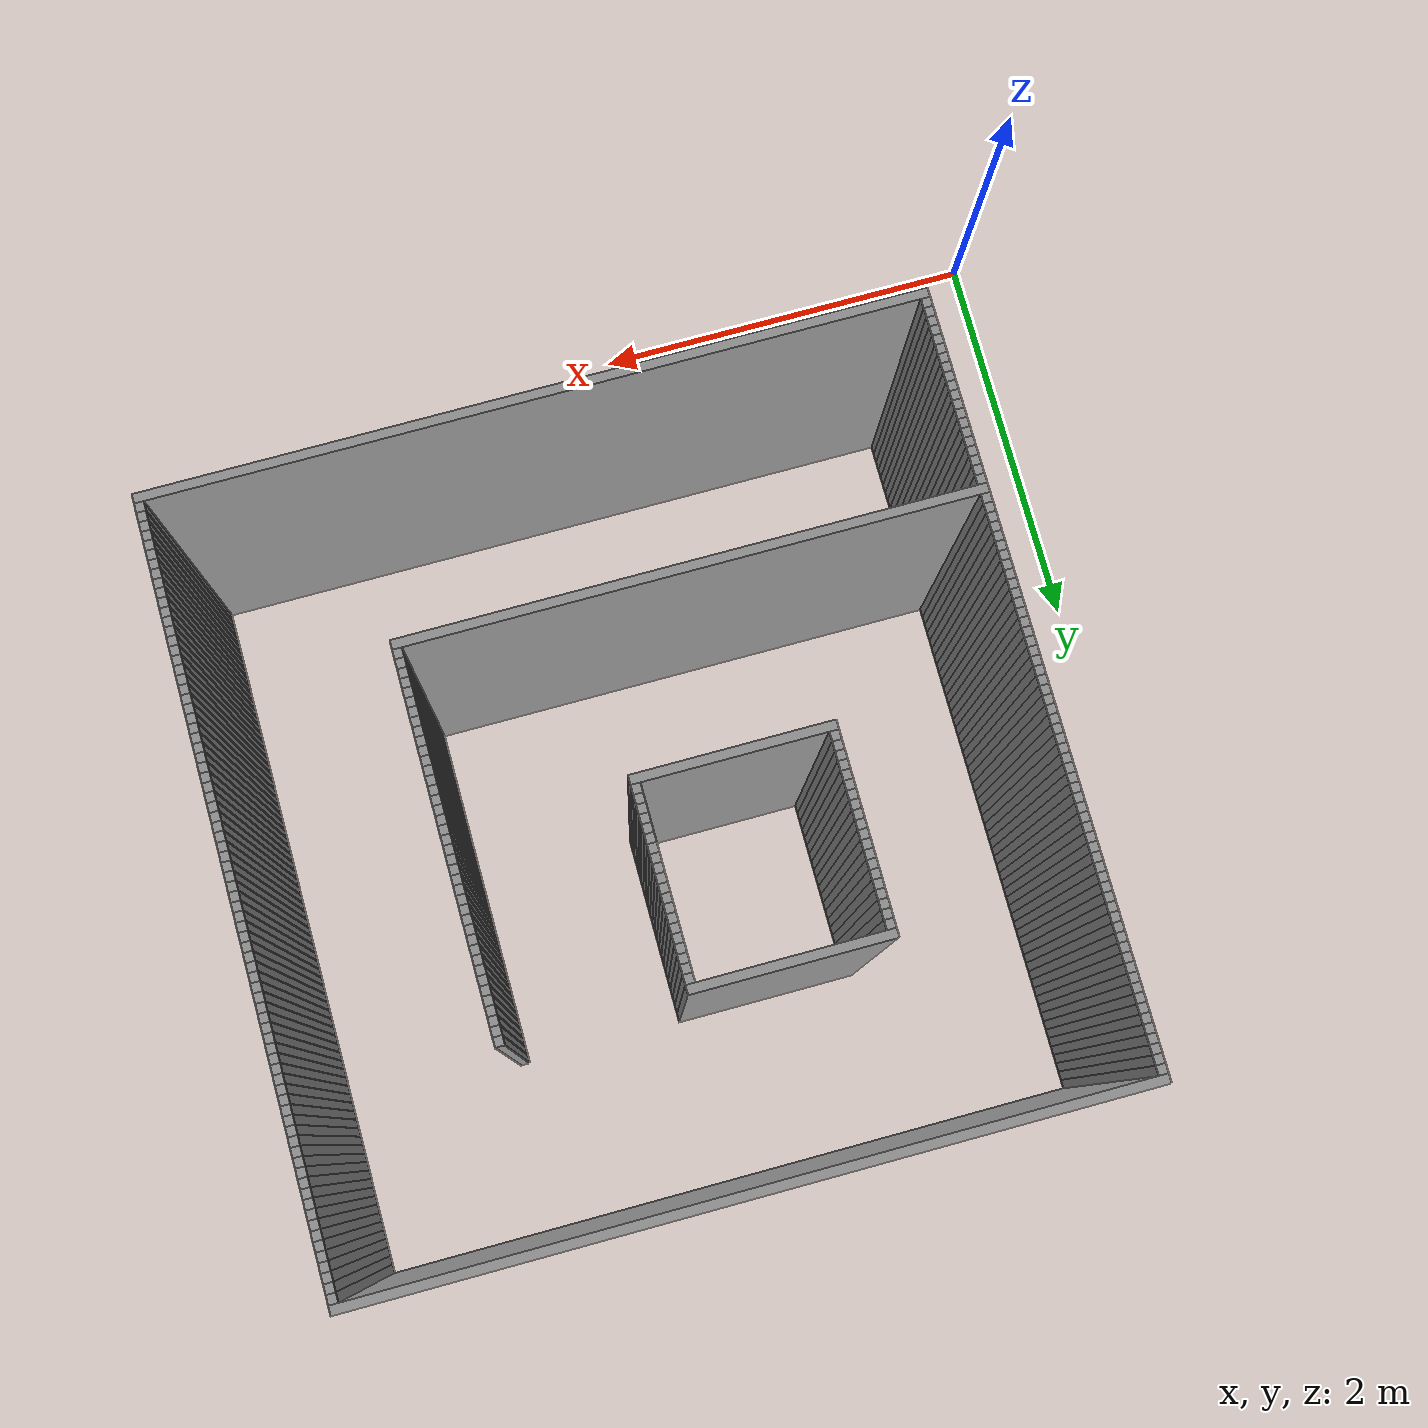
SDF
<?xml version='1.0'?>
<sdf version='1.6'>
    <model name='turtlebot3_rooms'>
    <pose frame=''>0 0 0 0 0 0</pose>

        <link name='Wall_0'>
            <collision name='Wall_0_Collision'>
            <geometry>
                <box>
                <size>4.1 0.05 2.5</size>
                </box>
            </geometry>
            <pose frame=''>0 0 0 0 0 0</pose>
            </collision>
            <visual name='Wall_0_Visual'>
            <pose frame=''>0 0 0 0 0 0</pose>
            <geometry>
                <box>
                <size>4.1 0.05 2.5</size>
                </box>
            </geometry>
            <material>
                <script>
                <uri>file://media/materials/scripts/gazebo.material</uri>
                <name>Gazebo/Grey</name>
                </script>
                <ambient>1 1 1 1</ambient>
            </material>
            </visual>
            <pose frame=''>2.5 0.475 0 0 0 0</pose>
        </link>

        <link name='Wall_1'>
            <collision name='Wall_1_Collision'>
            <geometry>
                <box>
                <size>0.05 0.05 2.5</size>
                </box>
            </geometry>
            <pose frame=''>0 0 0 0 0 0</pose>
            </collision>
            <visual name='Wall_1_Visual'>
            <pose frame=''>0 0 0 0 0 0</pose>
            <geometry>
                <box>
                <size>0.05 0.05 2.5</size>
                </box>
            </geometry>
            <material>
                <script>
                <uri>file://media/materials/scripts/gazebo.material</uri>
                <name>Gazebo/Grey</name>
                </script>
                <ambient>1 1 1 1</ambient>
            </material>
            </visual>
            <pose frame=''>0.475 0.525 0 0 0 0</pose>
        </link>

        <link name='Wall_2'>
            <collision name='Wall_2_Collision'>
            <geometry>
                <box>
                <size>0.05 0.05 2.5</size>
                </box>
            </geometry>
            <pose frame=''>0 0 0 0 0 0</pose>
            </collision>
            <visual name='Wall_2_Visual'>
            <pose frame=''>0 0 0 0 0 0</pose>
            <geometry>
                <box>
                <size>0.05 0.05 2.5</size>
                </box>
            </geometry>
            <material>
                <script>
                <uri>file://media/materials/scripts/gazebo.material</uri>
                <name>Gazebo/Grey</name>
                </script>
                <ambient>1 1 1 1</ambient>
            </material>
            </visual>
            <pose frame=''>4.525 0.525 0 0 0 0</pose>
        </link>

        <link name='Wall_3'>
            <collision name='Wall_3_Collision'>
            <geometry>
                <box>
                <size>0.05 0.05 2.5</size>
                </box>
            </geometry>
            <pose frame=''>0 0 0 0 0 0</pose>
            </collision>
            <visual name='Wall_3_Visual'>
            <pose frame=''>0 0 0 0 0 0</pose>
            <geometry>
                <box>
                <size>0.05 0.05 2.5</size>
                </box>
            </geometry>
            <material>
                <script>
                <uri>file://media/materials/scripts/gazebo.material</uri>
                <name>Gazebo/Grey</name>
                </script>
                <ambient>1 1 1 1</ambient>
            </material>
            </visual>
            <pose frame=''>0.475 0.575 0 0 0 0</pose>
        </link>

        <link name='Wall_4'>
            <collision name='Wall_4_Collision'>
            <geometry>
                <box>
                <size>0.05 0.05 2.5</size>
                </box>
            </geometry>
            <pose frame=''>0 0 0 0 0 0</pose>
            </collision>
            <visual name='Wall_4_Visual'>
            <pose frame=''>0 0 0 0 0 0</pose>
            <geometry>
                <box>
                <size>0.05 0.05 2.5</size>
                </box>
            </geometry>
            <material>
                <script>
                <uri>file://media/materials/scripts/gazebo.material</uri>
                <name>Gazebo/Grey</name>
                </script>
                <ambient>1 1 1 1</ambient>
            </material>
            </visual>
            <pose frame=''>4.525 0.575 0 0 0 0</pose>
        </link>

        <link name='Wall_5'>
            <collision name='Wall_5_Collision'>
            <geometry>
                <box>
                <size>0.05 0.05 2.5</size>
                </box>
            </geometry>
            <pose frame=''>0 0 0 0 0 0</pose>
            </collision>
            <visual name='Wall_5_Visual'>
            <pose frame=''>0 0 0 0 0 0</pose>
            <geometry>
                <box>
                <size>0.05 0.05 2.5</size>
                </box>
            </geometry>
            <material>
                <script>
                <uri>file://media/materials/scripts/gazebo.material</uri>
                <name>Gazebo/Grey</name>
                </script>
                <ambient>1 1 1 1</ambient>
            </material>
            </visual>
            <pose frame=''>0.475 0.625 0 0 0 0</pose>
        </link>

        <link name='Wall_6'>
            <collision name='Wall_6_Collision'>
            <geometry>
                <box>
                <size>0.05 0.05 2.5</size>
                </box>
            </geometry>
            <pose frame=''>0 0 0 0 0 0</pose>
            </collision>
            <visual name='Wall_6_Visual'>
            <pose frame=''>0 0 0 0 0 0</pose>
            <geometry>
                <box>
                <size>0.05 0.05 2.5</size>
                </box>
            </geometry>
            <material>
                <script>
                <uri>file://media/materials/scripts/gazebo.material</uri>
                <name>Gazebo/Grey</name>
                </script>
                <ambient>1 1 1 1</ambient>
            </material>
            </visual>
            <pose frame=''>4.525 0.625 0 0 0 0</pose>
        </link>

        <link name='Wall_7'>
            <collision name='Wall_7_Collision'>
            <geometry>
                <box>
                <size>0.05 0.05 2.5</size>
                </box>
            </geometry>
            <pose frame=''>0 0 0 0 0 0</pose>
            </collision>
            <visual name='Wall_7_Visual'>
            <pose frame=''>0 0 0 0 0 0</pose>
            <geometry>
                <box>
                <size>0.05 0.05 2.5</size>
                </box>
            </geometry>
            <material>
                <script>
                <uri>file://media/materials/scripts/gazebo.material</uri>
                <name>Gazebo/Grey</name>
                </script>
                <ambient>1 1 1 1</ambient>
            </material>
            </visual>
            <pose frame=''>0.475 0.675 0 0 0 0</pose>
        </link>

        <link name='Wall_8'>
            <collision name='Wall_8_Collision'>
            <geometry>
                <box>
                <size>0.05 0.05 2.5</size>
                </box>
            </geometry>
            <pose frame=''>0 0 0 0 0 0</pose>
            </collision>
            <visual name='Wall_8_Visual'>
            <pose frame=''>0 0 0 0 0 0</pose>
            <geometry>
                <box>
                <size>0.05 0.05 2.5</size>
                </box>
            </geometry>
            <material>
                <script>
                <uri>file://media/materials/scripts/gazebo.material</uri>
                <name>Gazebo/Grey</name>
                </script>
                <ambient>1 1 1 1</ambient>
            </material>
            </visual>
            <pose frame=''>4.525 0.675 0 0 0 0</pose>
        </link>

        <link name='Wall_9'>
            <collision name='Wall_9_Collision'>
            <geometry>
                <box>
                <size>0.05 0.05 2.5</size>
                </box>
            </geometry>
            <pose frame=''>0 0 0 0 0 0</pose>
            </collision>
            <visual name='Wall_9_Visual'>
            <pose frame=''>0 0 0 0 0 0</pose>
            <geometry>
                <box>
                <size>0.05 0.05 2.5</size>
                </box>
            </geometry>
            <material>
                <script>
                <uri>file://media/materials/scripts/gazebo.material</uri>
                <name>Gazebo/Grey</name>
                </script>
                <ambient>1 1 1 1</ambient>
            </material>
            </visual>
            <pose frame=''>0.475 0.725 0 0 0 0</pose>
        </link>

        <link name='Wall_10'>
            <collision name='Wall_10_Collision'>
            <geometry>
                <box>
                <size>0.05 0.05 2.5</size>
                </box>
            </geometry>
            <pose frame=''>0 0 0 0 0 0</pose>
            </collision>
            <visual name='Wall_10_Visual'>
            <pose frame=''>0 0 0 0 0 0</pose>
            <geometry>
                <box>
                <size>0.05 0.05 2.5</size>
                </box>
            </geometry>
            <material>
                <script>
                <uri>file://media/materials/scripts/gazebo.material</uri>
                <name>Gazebo/Grey</name>
                </script>
                <ambient>1 1 1 1</ambient>
            </material>
            </visual>
            <pose frame=''>4.525 0.725 0 0 0 0</pose>
        </link>

        <link name='Wall_11'>
            <collision name='Wall_11_Collision'>
            <geometry>
                <box>
                <size>0.05 0.05 2.5</size>
                </box>
            </geometry>
            <pose frame=''>0 0 0 0 0 0</pose>
            </collision>
            <visual name='Wall_11_Visual'>
            <pose frame=''>0 0 0 0 0 0</pose>
            <geometry>
                <box>
                <size>0.05 0.05 2.5</size>
                </box>
            </geometry>
            <material>
                <script>
                <uri>file://media/materials/scripts/gazebo.material</uri>
                <name>Gazebo/Grey</name>
                </script>
                <ambient>1 1 1 1</ambient>
            </material>
            </visual>
            <pose frame=''>0.475 0.775 0 0 0 0</pose>
        </link>

        <link name='Wall_12'>
            <collision name='Wall_12_Collision'>
            <geometry>
                <box>
                <size>0.05 0.05 2.5</size>
                </box>
            </geometry>
            <pose frame=''>0 0 0 0 0 0</pose>
            </collision>
            <visual name='Wall_12_Visual'>
            <pose frame=''>0 0 0 0 0 0</pose>
            <geometry>
                <box>
                <size>0.05 0.05 2.5</size>
                </box>
            </geometry>
            <material>
                <script>
                <uri>file://media/materials/scripts/gazebo.material</uri>
                <name>Gazebo/Grey</name>
                </script>
                <ambient>1 1 1 1</ambient>
            </material>
            </visual>
            <pose frame=''>4.525 0.775 0 0 0 0</pose>
        </link>

        <link name='Wall_13'>
            <collision name='Wall_13_Collision'>
            <geometry>
                <box>
                <size>0.05 0.05 2.5</size>
                </box>
            </geometry>
            <pose frame=''>0 0 0 0 0 0</pose>
            </collision>
            <visual name='Wall_13_Visual'>
            <pose frame=''>0 0 0 0 0 0</pose>
            <geometry>
                <box>
                <size>0.05 0.05 2.5</size>
                </box>
            </geometry>
            <material>
                <script>
                <uri>file://media/materials/scripts/gazebo.material</uri>
                <name>Gazebo/Grey</name>
                </script>
                <ambient>1 1 1 1</ambient>
            </material>
            </visual>
            <pose frame=''>0.475 0.825 0 0 0 0</pose>
        </link>

        <link name='Wall_14'>
            <collision name='Wall_14_Collision'>
            <geometry>
                <box>
                <size>0.05 0.05 2.5</size>
                </box>
            </geometry>
            <pose frame=''>0 0 0 0 0 0</pose>
            </collision>
            <visual name='Wall_14_Visual'>
            <pose frame=''>0 0 0 0 0 0</pose>
            <geometry>
                <box>
                <size>0.05 0.05 2.5</size>
                </box>
            </geometry>
            <material>
                <script>
                <uri>file://media/materials/scripts/gazebo.material</uri>
                <name>Gazebo/Grey</name>
                </script>
                <ambient>1 1 1 1</ambient>
            </material>
            </visual>
            <pose frame=''>4.525 0.825 0 0 0 0</pose>
        </link>

        <link name='Wall_15'>
            <collision name='Wall_15_Collision'>
            <geometry>
                <box>
                <size>0.05 0.05 2.5</size>
                </box>
            </geometry>
            <pose frame=''>0 0 0 0 0 0</pose>
            </collision>
            <visual name='Wall_15_Visual'>
            <pose frame=''>0 0 0 0 0 0</pose>
            <geometry>
                <box>
                <size>0.05 0.05 2.5</size>
                </box>
            </geometry>
            <material>
                <script>
                <uri>file://media/materials/scripts/gazebo.material</uri>
                <name>Gazebo/Grey</name>
                </script>
                <ambient>1 1 1 1</ambient>
            </material>
            </visual>
            <pose frame=''>0.475 0.875 0 0 0 0</pose>
        </link>

        <link name='Wall_16'>
            <collision name='Wall_16_Collision'>
            <geometry>
                <box>
                <size>0.05 0.05 2.5</size>
                </box>
            </geometry>
            <pose frame=''>0 0 0 0 0 0</pose>
            </collision>
            <visual name='Wall_16_Visual'>
            <pose frame=''>0 0 0 0 0 0</pose>
            <geometry>
                <box>
                <size>0.05 0.05 2.5</size>
                </box>
            </geometry>
            <material>
                <script>
                <uri>file://media/materials/scripts/gazebo.material</uri>
                <name>Gazebo/Grey</name>
                </script>
                <ambient>1 1 1 1</ambient>
            </material>
            </visual>
            <pose frame=''>4.525 0.875 0 0 0 0</pose>
        </link>

        <link name='Wall_17'>
            <collision name='Wall_17_Collision'>
            <geometry>
                <box>
                <size>0.05 0.05 2.5</size>
                </box>
            </geometry>
            <pose frame=''>0 0 0 0 0 0</pose>
            </collision>
            <visual name='Wall_17_Visual'>
            <pose frame=''>0 0 0 0 0 0</pose>
            <geometry>
                <box>
                <size>0.05 0.05 2.5</size>
                </box>
            </geometry>
            <material>
                <script>
                <uri>file://media/materials/scripts/gazebo.material</uri>
                <name>Gazebo/Grey</name>
                </script>
                <ambient>1 1 1 1</ambient>
            </material>
            </visual>
            <pose frame=''>0.475 0.925 0 0 0 0</pose>
        </link>

        <link name='Wall_18'>
            <collision name='Wall_18_Collision'>
            <geometry>
                <box>
                <size>0.05 0.05 2.5</size>
                </box>
            </geometry>
            <pose frame=''>0 0 0 0 0 0</pose>
            </collision>
            <visual name='Wall_18_Visual'>
            <pose frame=''>0 0 0 0 0 0</pose>
            <geometry>
                <box>
                <size>0.05 0.05 2.5</size>
                </box>
            </geometry>
            <material>
                <script>
                <uri>file://media/materials/scripts/gazebo.material</uri>
                <name>Gazebo/Grey</name>
                </script>
                <ambient>1 1 1 1</ambient>
            </material>
            </visual>
            <pose frame=''>4.525 0.925 0 0 0 0</pose>
        </link>

        <link name='Wall_19'>
            <collision name='Wall_19_Collision'>
            <geometry>
                <box>
                <size>0.05 0.05 2.5</size>
                </box>
            </geometry>
            <pose frame=''>0 0 0 0 0 0</pose>
            </collision>
            <visual name='Wall_19_Visual'>
            <pose frame=''>0 0 0 0 0 0</pose>
            <geometry>
                <box>
                <size>0.05 0.05 2.5</size>
                </box>
            </geometry>
            <material>
                <script>
                <uri>file://media/materials/scripts/gazebo.material</uri>
                <name>Gazebo/Grey</name>
                </script>
                <ambient>1 1 1 1</ambient>
            </material>
            </visual>
            <pose frame=''>0.475 0.975 0 0 0 0</pose>
        </link>

        <link name='Wall_20'>
            <collision name='Wall_20_Collision'>
            <geometry>
                <box>
                <size>0.05 0.05 2.5</size>
                </box>
            </geometry>
            <pose frame=''>0 0 0 0 0 0</pose>
            </collision>
            <visual name='Wall_20_Visual'>
            <pose frame=''>0 0 0 0 0 0</pose>
            <geometry>
                <box>
                <size>0.05 0.05 2.5</size>
                </box>
            </geometry>
            <material>
                <script>
                <uri>file://media/materials/scripts/gazebo.material</uri>
                <name>Gazebo/Grey</name>
                </script>
                <ambient>1 1 1 1</ambient>
            </material>
            </visual>
            <pose frame=''>4.525 0.975 0 0 0 0</pose>
        </link>

        <link name='Wall_21'>
            <collision name='Wall_21_Collision'>
            <geometry>
                <box>
                <size>0.05 0.05 2.5</size>
                </box>
            </geometry>
            <pose frame=''>0 0 0 0 0 0</pose>
            </collision>
            <visual name='Wall_21_Visual'>
            <pose frame=''>0 0 0 0 0 0</pose>
            <geometry>
                <box>
                <size>0.05 0.05 2.5</size>
                </box>
            </geometry>
            <material>
                <script>
                <uri>file://media/materials/scripts/gazebo.material</uri>
                <name>Gazebo/Grey</name>
                </script>
                <ambient>1 1 1 1</ambient>
            </material>
            </visual>
            <pose frame=''>0.475 1.025 0 0 0 0</pose>
        </link>

        <link name='Wall_22'>
            <collision name='Wall_22_Collision'>
            <geometry>
                <box>
                <size>0.05 0.05 2.5</size>
                </box>
            </geometry>
            <pose frame=''>0 0 0 0 0 0</pose>
            </collision>
            <visual name='Wall_22_Visual'>
            <pose frame=''>0 0 0 0 0 0</pose>
            <geometry>
                <box>
                <size>0.05 0.05 2.5</size>
                </box>
            </geometry>
            <material>
                <script>
                <uri>file://media/materials/scripts/gazebo.material</uri>
                <name>Gazebo/Grey</name>
                </script>
                <ambient>1 1 1 1</ambient>
            </material>
            </visual>
            <pose frame=''>4.525 1.025 0 0 0 0</pose>
        </link>

        <link name='Wall_23'>
            <collision name='Wall_23_Collision'>
            <geometry>
                <box>
                <size>0.05 0.05 2.5</size>
                </box>
            </geometry>
            <pose frame=''>0 0 0 0 0 0</pose>
            </collision>
            <visual name='Wall_23_Visual'>
            <pose frame=''>0 0 0 0 0 0</pose>
            <geometry>
                <box>
                <size>0.05 0.05 2.5</size>
                </box>
            </geometry>
            <material>
                <script>
                <uri>file://media/materials/scripts/gazebo.material</uri>
                <name>Gazebo/Grey</name>
                </script>
                <ambient>1 1 1 1</ambient>
            </material>
            </visual>
            <pose frame=''>0.475 1.075 0 0 0 0</pose>
        </link>

        <link name='Wall_24'>
            <collision name='Wall_24_Collision'>
            <geometry>
                <box>
                <size>0.05 0.05 2.5</size>
                </box>
            </geometry>
            <pose frame=''>0 0 0 0 0 0</pose>
            </collision>
            <visual name='Wall_24_Visual'>
            <pose frame=''>0 0 0 0 0 0</pose>
            <geometry>
                <box>
                <size>0.05 0.05 2.5</size>
                </box>
            </geometry>
            <material>
                <script>
                <uri>file://media/materials/scripts/gazebo.material</uri>
                <name>Gazebo/Grey</name>
                </script>
                <ambient>1 1 1 1</ambient>
            </material>
            </visual>
            <pose frame=''>4.525 1.075 0 0 0 0</pose>
        </link>

        <link name='Wall_25'>
            <collision name='Wall_25_Collision'>
            <geometry>
                <box>
                <size>0.05 0.05 2.5</size>
                </box>
            </geometry>
            <pose frame=''>0 0 0 0 0 0</pose>
            </collision>
            <visual name='Wall_25_Visual'>
            <pose frame=''>0 0 0 0 0 0</pose>
            <geometry>
                <box>
                <size>0.05 0.05 2.5</size>
                </box>
            </geometry>
            <material>
                <script>
                <uri>file://media/materials/scripts/gazebo.material</uri>
                <name>Gazebo/Grey</name>
                </script>
                <ambient>1 1 1 1</ambient>
            </material>
            </visual>
            <pose frame=''>0.475 1.125 0 0 0 0</pose>
        </link>

        <link name='Wall_26'>
            <collision name='Wall_26_Collision'>
            <geometry>
                <box>
                <size>0.05 0.05 2.5</size>
                </box>
            </geometry>
            <pose frame=''>0 0 0 0 0 0</pose>
            </collision>
            <visual name='Wall_26_Visual'>
            <pose frame=''>0 0 0 0 0 0</pose>
            <geometry>
                <box>
                <size>0.05 0.05 2.5</size>
                </box>
            </geometry>
            <material>
                <script>
                <uri>file://media/materials/scripts/gazebo.material</uri>
                <name>Gazebo/Grey</name>
                </script>
                <ambient>1 1 1 1</ambient>
            </material>
            </visual>
            <pose frame=''>4.525 1.125 0 0 0 0</pose>
        </link>

        <link name='Wall_27'>
            <collision name='Wall_27_Collision'>
            <geometry>
                <box>
                <size>0.05 0.05 2.5</size>
                </box>
            </geometry>
            <pose frame=''>0 0 0 0 0 0</pose>
            </collision>
            <visual name='Wall_27_Visual'>
            <pose frame=''>0 0 0 0 0 0</pose>
            <geometry>
                <box>
                <size>0.05 0.05 2.5</size>
                </box>
            </geometry>
            <material>
                <script>
                <uri>file://media/materials/scripts/gazebo.material</uri>
                <name>Gazebo/Grey</name>
                </script>
                <ambient>1 1 1 1</ambient>
            </material>
            </visual>
            <pose frame=''>0.475 1.175 0 0 0 0</pose>
        </link>

        <link name='Wall_28'>
            <collision name='Wall_28_Collision'>
            <geometry>
                <box>
                <size>0.05 0.05 2.5</size>
                </box>
            </geometry>
            <pose frame=''>0 0 0 0 0 0</pose>
            </collision>
            <visual name='Wall_28_Visual'>
            <pose frame=''>0 0 0 0 0 0</pose>
            <geometry>
                <box>
                <size>0.05 0.05 2.5</size>
                </box>
            </geometry>
            <material>
                <script>
                <uri>file://media/materials/scripts/gazebo.material</uri>
                <name>Gazebo/Grey</name>
                </script>
                <ambient>1 1 1 1</ambient>
            </material>
            </visual>
            <pose frame=''>4.525 1.175 0 0 0 0</pose>
        </link>

        <link name='Wall_29'>
            <collision name='Wall_29_Collision'>
            <geometry>
                <box>
                <size>0.05 0.05 2.5</size>
                </box>
            </geometry>
            <pose frame=''>0 0 0 0 0 0</pose>
            </collision>
            <visual name='Wall_29_Visual'>
            <pose frame=''>0 0 0 0 0 0</pose>
            <geometry>
                <box>
                <size>0.05 0.05 2.5</size>
                </box>
            </geometry>
            <material>
                <script>
                <uri>file://media/materials/scripts/gazebo.material</uri>
                <name>Gazebo/Grey</name>
                </script>
                <ambient>1 1 1 1</ambient>
            </material>
            </visual>
            <pose frame=''>0.475 1.225 0 0 0 0</pose>
        </link>

        <link name='Wall_30'>
            <collision name='Wall_30_Collision'>
            <geometry>
                <box>
                <size>0.05 0.05 2.5</size>
                </box>
            </geometry>
            <pose frame=''>0 0 0 0 0 0</pose>
            </collision>
            <visual name='Wall_30_Visual'>
            <pose frame=''>0 0 0 0 0 0</pose>
            <geometry>
                <box>
                <size>0.05 0.05 2.5</size>
                </box>
            </geometry>
            <material>
                <script>
                <uri>file://media/materials/scripts/gazebo.material</uri>
                <name>Gazebo/Grey</name>
                </script>
                <ambient>1 1 1 1</ambient>
            </material>
            </visual>
            <pose frame=''>4.525 1.225 0 0 0 0</pose>
        </link>

        <link name='Wall_31'>
            <collision name='Wall_31_Collision'>
            <geometry>
                <box>
                <size>0.05 0.05 2.5</size>
                </box>
            </geometry>
            <pose frame=''>0 0 0 0 0 0</pose>
            </collision>
            <visual name='Wall_31_Visual'>
            <pose frame=''>0 0 0 0 0 0</pose>
            <geometry>
                <box>
                <size>0.05 0.05 2.5</size>
                </box>
            </geometry>
            <material>
                <script>
                <uri>file://media/materials/scripts/gazebo.material</uri>
                <name>Gazebo/Grey</name>
                </script>
                <ambient>1 1 1 1</ambient>
            </material>
            </visual>
            <pose frame=''>0.475 1.275 0 0 0 0</pose>
        </link>

        <link name='Wall_32'>
            <collision name='Wall_32_Collision'>
            <geometry>
                <box>
                <size>0.05 0.05 2.5</size>
                </box>
            </geometry>
            <pose frame=''>0 0 0 0 0 0</pose>
            </collision>
            <visual name='Wall_32_Visual'>
            <pose frame=''>0 0 0 0 0 0</pose>
            <geometry>
                <box>
                <size>0.05 0.05 2.5</size>
                </box>
            </geometry>
            <material>
                <script>
                <uri>file://media/materials/scripts/gazebo.material</uri>
                <name>Gazebo/Grey</name>
                </script>
                <ambient>1 1 1 1</ambient>
            </material>
            </visual>
            <pose frame=''>4.525 1.275 0 0 0 0</pose>
        </link>

        <link name='Wall_33'>
            <collision name='Wall_33_Collision'>
            <geometry>
                <box>
                <size>0.05 0.05 2.5</size>
                </box>
            </geometry>
            <pose frame=''>0 0 0 0 0 0</pose>
            </collision>
            <visual name='Wall_33_Visual'>
            <pose frame=''>0 0 0 0 0 0</pose>
            <geometry>
                <box>
                <size>0.05 0.05 2.5</size>
                </box>
            </geometry>
            <material>
                <script>
                <uri>file://media/materials/scripts/gazebo.material</uri>
                <name>Gazebo/Grey</name>
                </script>
                <ambient>1 1 1 1</ambient>
            </material>
            </visual>
            <pose frame=''>0.475 1.325 0 0 0 0</pose>
        </link>

        <link name='Wall_34'>
            <collision name='Wall_34_Collision'>
            <geometry>
                <box>
                <size>0.05 0.05 2.5</size>
                </box>
            </geometry>
            <pose frame=''>0 0 0 0 0 0</pose>
            </collision>
            <visual name='Wall_34_Visual'>
            <pose frame=''>0 0 0 0 0 0</pose>
            <geometry>
                <box>
                <size>0.05 0.05 2.5</size>
                </box>
            </geometry>
            <material>
                <script>
                <uri>file://media/materials/scripts/gazebo.material</uri>
                <name>Gazebo/Grey</name>
                </script>
                <ambient>1 1 1 1</ambient>
            </material>
            </visual>
            <pose frame=''>4.525 1.325 0 0 0 0</pose>
        </link>

        <link name='Wall_35'>
            <collision name='Wall_35_Collision'>
            <geometry>
                <box>
                <size>0.05 0.05 2.5</size>
                </box>
            </geometry>
            <pose frame=''>0 0 0 0 0 0</pose>
            </collision>
            <visual name='Wall_35_Visual'>
            <pose frame=''>0 0 0 0 0 0</pose>
            <geometry>
                <box>
                <size>0.05 0.05 2.5</size>
                </box>
            </geometry>
            <material>
                <script>
                <uri>file://media/materials/scripts/gazebo.material</uri>
                <name>Gazebo/Grey</name>
                </script>
                <ambient>1 1 1 1</ambient>
            </material>
            </visual>
            <pose frame=''>0.475 1.375 0 0 0 0</pose>
        </link>

        <link name='Wall_36'>
            <collision name='Wall_36_Collision'>
            <geometry>
                <box>
                <size>0.05 0.05 2.5</size>
                </box>
            </geometry>
            <pose frame=''>0 0 0 0 0 0</pose>
            </collision>
            <visual name='Wall_36_Visual'>
            <pose frame=''>0 0 0 0 0 0</pose>
            <geometry>
                <box>
                <size>0.05 0.05 2.5</size>
                </box>
            </geometry>
            <material>
                <script>
                <uri>file://media/materials/scripts/gazebo.material</uri>
                <name>Gazebo/Grey</name>
                </script>
                <ambient>1 1 1 1</ambient>
            </material>
            </visual>
            <pose frame=''>4.525 1.375 0 0 0 0</pose>
        </link>

        <link name='Wall_37'>
            <collision name='Wall_37_Collision'>
            <geometry>
                <box>
                <size>0.05 0.05 2.5</size>
                </box>
            </geometry>
            <pose frame=''>0 0 0 0 0 0</pose>
            </collision>
            <visual name='Wall_37_Visual'>
            <pose frame=''>0 0 0 0 0 0</pose>
            <geometry>
                <box>
                <size>0.05 0.05 2.5</size>
                </box>
            </geometry>
            <material>
                <script>
                <uri>file://media/materials/scripts/gazebo.material</uri>
                <name>Gazebo/Grey</name>
                </script>
                <ambient>1 1 1 1</ambient>
            </material>
            </visual>
            <pose frame=''>0.475 1.425 0 0 0 0</pose>
        </link>

        <link name='Wall_38'>
            <collision name='Wall_38_Collision'>
            <geometry>
                <box>
                <size>0.05 0.05 2.5</size>
                </box>
            </geometry>
            <pose frame=''>0 0 0 0 0 0</pose>
            </collision>
            <visual name='Wall_38_Visual'>
            <pose frame=''>0 0 0 0 0 0</pose>
            <geometry>
                <box>
                <size>0.05 0.05 2.5</size>
                </box>
            </geometry>
            <material>
                <script>
                <uri>file://media/materials/scripts/gazebo.material</uri>
                <name>Gazebo/Grey</name>
                </script>
                <ambient>1 1 1 1</ambient>
            </material>
            </visual>
            <pose frame=''>4.525 1.425 0 0 0 0</pose>
        </link>

        <link name='Wall_39'>
            <collision name='Wall_39_Collision'>
            <geometry>
                <box>
                <size>0.05 0.05 2.5</size>
                </box>
            </geometry>
            <pose frame=''>0 0 0 0 0 0</pose>
            </collision>
            <visual name='Wall_39_Visual'>
            <pose frame=''>0 0 0 0 0 0</pose>
            <geometry>
                <box>
                <size>0.05 0.05 2.5</size>
                </box>
            </geometry>
            <material>
                <script>
                <uri>file://media/materials/scripts/gazebo.material</uri>
                <name>Gazebo/Grey</name>
                </script>
                <ambient>1 1 1 1</ambient>
            </material>
            </visual>
            <pose frame=''>0.475 1.475 0 0 0 0</pose>
        </link>

        <link name='Wall_40'>
            <collision name='Wall_40_Collision'>
            <geometry>
                <box>
                <size>0.05 0.05 2.5</size>
                </box>
            </geometry>
            <pose frame=''>0 0 0 0 0 0</pose>
            </collision>
            <visual name='Wall_40_Visual'>
            <pose frame=''>0 0 0 0 0 0</pose>
            <geometry>
                <box>
                <size>0.05 0.05 2.5</size>
                </box>
            </geometry>
            <material>
                <script>
                <uri>file://media/materials/scripts/gazebo.material</uri>
                <name>Gazebo/Grey</name>
                </script>
                <ambient>1 1 1 1</ambient>
            </material>
            </visual>
            <pose frame=''>4.525 1.475 0 0 0 0</pose>
        </link>

        <link name='Wall_41'>
            <collision name='Wall_41_Collision'>
            <geometry>
                <box>
                <size>3.05 0.05 2.5</size>
                </box>
            </geometry>
            <pose frame=''>0 0 0 0 0 0</pose>
            </collision>
            <visual name='Wall_41_Visual'>
            <pose frame=''>0 0 0 0 0 0</pose>
            <geometry>
                <box>
                <size>3.05 0.05 2.5</size>
                </box>
            </geometry>
            <material>
                <script>
                <uri>file://media/materials/scripts/gazebo.material</uri>
                <name>Gazebo/Grey</name>
                </script>
                <ambient>1 1 1 1</ambient>
            </material>
            </visual>
            <pose frame=''>1.975 1.525 0 0 0 0</pose>
        </link>

        <link name='Wall_42'>
            <collision name='Wall_42_Collision'>
            <geometry>
                <box>
                <size>0.05 0.05 2.5</size>
                </box>
            </geometry>
            <pose frame=''>0 0 0 0 0 0</pose>
            </collision>
            <visual name='Wall_42_Visual'>
            <pose frame=''>0 0 0 0 0 0</pose>
            <geometry>
                <box>
                <size>0.05 0.05 2.5</size>
                </box>
            </geometry>
            <material>
                <script>
                <uri>file://media/materials/scripts/gazebo.material</uri>
                <name>Gazebo/Grey</name>
                </script>
                <ambient>1 1 1 1</ambient>
            </material>
            </visual>
            <pose frame=''>4.525 1.525 0 0 0 0</pose>
        </link>

        <link name='Wall_43'>
            <collision name='Wall_43_Collision'>
            <geometry>
                <box>
                <size>0.05 0.05 2.5</size>
                </box>
            </geometry>
            <pose frame=''>0 0 0 0 0 0</pose>
            </collision>
            <visual name='Wall_43_Visual'>
            <pose frame=''>0 0 0 0 0 0</pose>
            <geometry>
                <box>
                <size>0.05 0.05 2.5</size>
                </box>
            </geometry>
            <material>
                <script>
                <uri>file://media/materials/scripts/gazebo.material</uri>
                <name>Gazebo/Grey</name>
                </script>
                <ambient>1 1 1 1</ambient>
            </material>
            </visual>
            <pose frame=''>0.475 1.575 0 0 0 0</pose>
        </link>

        <link name='Wall_44'>
            <collision name='Wall_44_Collision'>
            <geometry>
                <box>
                <size>0.05 0.05 2.5</size>
                </box>
            </geometry>
            <pose frame=''>0 0 0 0 0 0</pose>
            </collision>
            <visual name='Wall_44_Visual'>
            <pose frame=''>0 0 0 0 0 0</pose>
            <geometry>
                <box>
                <size>0.05 0.05 2.5</size>
                </box>
            </geometry>
            <material>
                <script>
                <uri>file://media/materials/scripts/gazebo.material</uri>
                <name>Gazebo/Grey</name>
                </script>
                <ambient>1 1 1 1</ambient>
            </material>
            </visual>
            <pose frame=''>3.475 1.575 0 0 0 0</pose>
        </link>

        <link name='Wall_45'>
            <collision name='Wall_45_Collision'>
            <geometry>
                <box>
                <size>0.05 0.05 2.5</size>
                </box>
            </geometry>
            <pose frame=''>0 0 0 0 0 0</pose>
            </collision>
            <visual name='Wall_45_Visual'>
            <pose frame=''>0 0 0 0 0 0</pose>
            <geometry>
                <box>
                <size>0.05 0.05 2.5</size>
                </box>
            </geometry>
            <material>
                <script>
                <uri>file://media/materials/scripts/gazebo.material</uri>
                <name>Gazebo/Grey</name>
                </script>
                <ambient>1 1 1 1</ambient>
            </material>
            </visual>
            <pose frame=''>4.525 1.575 0 0 0 0</pose>
        </link>

        <link name='Wall_46'>
            <collision name='Wall_46_Collision'>
            <geometry>
                <box>
                <size>0.05 0.05 2.5</size>
                </box>
            </geometry>
            <pose frame=''>0 0 0 0 0 0</pose>
            </collision>
            <visual name='Wall_46_Visual'>
            <pose frame=''>0 0 0 0 0 0</pose>
            <geometry>
                <box>
                <size>0.05 0.05 2.5</size>
                </box>
            </geometry>
            <material>
                <script>
                <uri>file://media/materials/scripts/gazebo.material</uri>
                <name>Gazebo/Grey</name>
                </script>
                <ambient>1 1 1 1</ambient>
            </material>
            </visual>
            <pose frame=''>0.475 1.625 0 0 0 0</pose>
        </link>

        <link name='Wall_47'>
            <collision name='Wall_47_Collision'>
            <geometry>
                <box>
                <size>0.05 0.05 2.5</size>
                </box>
            </geometry>
            <pose frame=''>0 0 0 0 0 0</pose>
            </collision>
            <visual name='Wall_47_Visual'>
            <pose frame=''>0 0 0 0 0 0</pose>
            <geometry>
                <box>
                <size>0.05 0.05 2.5</size>
                </box>
            </geometry>
            <material>
                <script>
                <uri>file://media/materials/scripts/gazebo.material</uri>
                <name>Gazebo/Grey</name>
                </script>
                <ambient>1 1 1 1</ambient>
            </material>
            </visual>
            <pose frame=''>3.475 1.625 0 0 0 0</pose>
        </link>

        <link name='Wall_48'>
            <collision name='Wall_48_Collision'>
            <geometry>
                <box>
                <size>0.05 0.05 2.5</size>
                </box>
            </geometry>
            <pose frame=''>0 0 0 0 0 0</pose>
            </collision>
            <visual name='Wall_48_Visual'>
            <pose frame=''>0 0 0 0 0 0</pose>
            <geometry>
                <box>
                <size>0.05 0.05 2.5</size>
                </box>
            </geometry>
            <material>
                <script>
                <uri>file://media/materials/scripts/gazebo.material</uri>
                <name>Gazebo/Grey</name>
                </script>
                <ambient>1 1 1 1</ambient>
            </material>
            </visual>
            <pose frame=''>4.525 1.625 0 0 0 0</pose>
        </link>

        <link name='Wall_49'>
            <collision name='Wall_49_Collision'>
            <geometry>
                <box>
                <size>0.05 0.05 2.5</size>
                </box>
            </geometry>
            <pose frame=''>0 0 0 0 0 0</pose>
            </collision>
            <visual name='Wall_49_Visual'>
            <pose frame=''>0 0 0 0 0 0</pose>
            <geometry>
                <box>
                <size>0.05 0.05 2.5</size>
                </box>
            </geometry>
            <material>
                <script>
                <uri>file://media/materials/scripts/gazebo.material</uri>
                <name>Gazebo/Grey</name>
                </script>
                <ambient>1 1 1 1</ambient>
            </material>
            </visual>
            <pose frame=''>0.475 1.675 0 0 0 0</pose>
        </link>

        <link name='Wall_50'>
            <collision name='Wall_50_Collision'>
            <geometry>
                <box>
                <size>0.05 0.05 2.5</size>
                </box>
            </geometry>
            <pose frame=''>0 0 0 0 0 0</pose>
            </collision>
            <visual name='Wall_50_Visual'>
            <pose frame=''>0 0 0 0 0 0</pose>
            <geometry>
                <box>
                <size>0.05 0.05 2.5</size>
                </box>
            </geometry>
            <material>
                <script>
                <uri>file://media/materials/scripts/gazebo.material</uri>
                <name>Gazebo/Grey</name>
                </script>
                <ambient>1 1 1 1</ambient>
            </material>
            </visual>
            <pose frame=''>3.475 1.675 0 0 0 0</pose>
        </link>

        <link name='Wall_51'>
            <collision name='Wall_51_Collision'>
            <geometry>
                <box>
                <size>0.05 0.05 2.5</size>
                </box>
            </geometry>
            <pose frame=''>0 0 0 0 0 0</pose>
            </collision>
            <visual name='Wall_51_Visual'>
            <pose frame=''>0 0 0 0 0 0</pose>
            <geometry>
                <box>
                <size>0.05 0.05 2.5</size>
                </box>
            </geometry>
            <material>
                <script>
                <uri>file://media/materials/scripts/gazebo.material</uri>
                <name>Gazebo/Grey</name>
                </script>
                <ambient>1 1 1 1</ambient>
            </material>
            </visual>
            <pose frame=''>4.525 1.675 0 0 0 0</pose>
        </link>

        <link name='Wall_52'>
            <collision name='Wall_52_Collision'>
            <geometry>
                <box>
                <size>0.05 0.05 2.5</size>
                </box>
            </geometry>
            <pose frame=''>0 0 0 0 0 0</pose>
            </collision>
            <visual name='Wall_52_Visual'>
            <pose frame=''>0 0 0 0 0 0</pose>
            <geometry>
                <box>
                <size>0.05 0.05 2.5</size>
                </box>
            </geometry>
            <material>
                <script>
                <uri>file://media/materials/scripts/gazebo.material</uri>
                <name>Gazebo/Grey</name>
                </script>
                <ambient>1 1 1 1</ambient>
            </material>
            </visual>
            <pose frame=''>0.475 1.725 0 0 0 0</pose>
        </link>

        <link name='Wall_53'>
            <collision name='Wall_53_Collision'>
            <geometry>
                <box>
                <size>0.05 0.05 2.5</size>
                </box>
            </geometry>
            <pose frame=''>0 0 0 0 0 0</pose>
            </collision>
            <visual name='Wall_53_Visual'>
            <pose frame=''>0 0 0 0 0 0</pose>
            <geometry>
                <box>
                <size>0.05 0.05 2.5</size>
                </box>
            </geometry>
            <material>
                <script>
                <uri>file://media/materials/scripts/gazebo.material</uri>
                <name>Gazebo/Grey</name>
                </script>
                <ambient>1 1 1 1</ambient>
            </material>
            </visual>
            <pose frame=''>3.475 1.725 0 0 0 0</pose>
        </link>

        <link name='Wall_54'>
            <collision name='Wall_54_Collision'>
            <geometry>
                <box>
                <size>0.05 0.05 2.5</size>
                </box>
            </geometry>
            <pose frame=''>0 0 0 0 0 0</pose>
            </collision>
            <visual name='Wall_54_Visual'>
            <pose frame=''>0 0 0 0 0 0</pose>
            <geometry>
                <box>
                <size>0.05 0.05 2.5</size>
                </box>
            </geometry>
            <material>
                <script>
                <uri>file://media/materials/scripts/gazebo.material</uri>
                <name>Gazebo/Grey</name>
                </script>
                <ambient>1 1 1 1</ambient>
            </material>
            </visual>
            <pose frame=''>4.525 1.725 0 0 0 0</pose>
        </link>

        <link name='Wall_55'>
            <collision name='Wall_55_Collision'>
            <geometry>
                <box>
                <size>0.05 0.05 2.5</size>
                </box>
            </geometry>
            <pose frame=''>0 0 0 0 0 0</pose>
            </collision>
            <visual name='Wall_55_Visual'>
            <pose frame=''>0 0 0 0 0 0</pose>
            <geometry>
                <box>
                <size>0.05 0.05 2.5</size>
                </box>
            </geometry>
            <material>
                <script>
                <uri>file://media/materials/scripts/gazebo.material</uri>
                <name>Gazebo/Grey</name>
                </script>
                <ambient>1 1 1 1</ambient>
            </material>
            </visual>
            <pose frame=''>0.475 1.775 0 0 0 0</pose>
        </link>

        <link name='Wall_56'>
            <collision name='Wall_56_Collision'>
            <geometry>
                <box>
                <size>0.05 0.05 2.5</size>
                </box>
            </geometry>
            <pose frame=''>0 0 0 0 0 0</pose>
            </collision>
            <visual name='Wall_56_Visual'>
            <pose frame=''>0 0 0 0 0 0</pose>
            <geometry>
                <box>
                <size>0.05 0.05 2.5</size>
                </box>
            </geometry>
            <material>
                <script>
                <uri>file://media/materials/scripts/gazebo.material</uri>
                <name>Gazebo/Grey</name>
                </script>
                <ambient>1 1 1 1</ambient>
            </material>
            </visual>
            <pose frame=''>3.475 1.775 0 0 0 0</pose>
        </link>

        <link name='Wall_57'>
            <collision name='Wall_57_Collision'>
            <geometry>
                <box>
                <size>0.05 0.05 2.5</size>
                </box>
            </geometry>
            <pose frame=''>0 0 0 0 0 0</pose>
            </collision>
            <visual name='Wall_57_Visual'>
            <pose frame=''>0 0 0 0 0 0</pose>
            <geometry>
                <box>
                <size>0.05 0.05 2.5</size>
                </box>
            </geometry>
            <material>
                <script>
                <uri>file://media/materials/scripts/gazebo.material</uri>
                <name>Gazebo/Grey</name>
                </script>
                <ambient>1 1 1 1</ambient>
            </material>
            </visual>
            <pose frame=''>4.525 1.775 0 0 0 0</pose>
        </link>

        <link name='Wall_58'>
            <collision name='Wall_58_Collision'>
            <geometry>
                <box>
                <size>0.05 0.05 2.5</size>
                </box>
            </geometry>
            <pose frame=''>0 0 0 0 0 0</pose>
            </collision>
            <visual name='Wall_58_Visual'>
            <pose frame=''>0 0 0 0 0 0</pose>
            <geometry>
                <box>
                <size>0.05 0.05 2.5</size>
                </box>
            </geometry>
            <material>
                <script>
                <uri>file://media/materials/scripts/gazebo.material</uri>
                <name>Gazebo/Grey</name>
                </script>
                <ambient>1 1 1 1</ambient>
            </material>
            </visual>
            <pose frame=''>0.475 1.825 0 0 0 0</pose>
        </link>

        <link name='Wall_59'>
            <collision name='Wall_59_Collision'>
            <geometry>
                <box>
                <size>0.05 0.05 2.5</size>
                </box>
            </geometry>
            <pose frame=''>0 0 0 0 0 0</pose>
            </collision>
            <visual name='Wall_59_Visual'>
            <pose frame=''>0 0 0 0 0 0</pose>
            <geometry>
                <box>
                <size>0.05 0.05 2.5</size>
                </box>
            </geometry>
            <material>
                <script>
                <uri>file://media/materials/scripts/gazebo.material</uri>
                <name>Gazebo/Grey</name>
                </script>
                <ambient>1 1 1 1</ambient>
            </material>
            </visual>
            <pose frame=''>3.475 1.825 0 0 0 0</pose>
        </link>

        <link name='Wall_60'>
            <collision name='Wall_60_Collision'>
            <geometry>
                <box>
                <size>0.05 0.05 2.5</size>
                </box>
            </geometry>
            <pose frame=''>0 0 0 0 0 0</pose>
            </collision>
            <visual name='Wall_60_Visual'>
            <pose frame=''>0 0 0 0 0 0</pose>
            <geometry>
                <box>
                <size>0.05 0.05 2.5</size>
                </box>
            </geometry>
            <material>
                <script>
                <uri>file://media/materials/scripts/gazebo.material</uri>
                <name>Gazebo/Grey</name>
                </script>
                <ambient>1 1 1 1</ambient>
            </material>
            </visual>
            <pose frame=''>4.525 1.825 0 0 0 0</pose>
        </link>

        <link name='Wall_61'>
            <collision name='Wall_61_Collision'>
            <geometry>
                <box>
                <size>0.05 0.05 2.5</size>
                </box>
            </geometry>
            <pose frame=''>0 0 0 0 0 0</pose>
            </collision>
            <visual name='Wall_61_Visual'>
            <pose frame=''>0 0 0 0 0 0</pose>
            <geometry>
                <box>
                <size>0.05 0.05 2.5</size>
                </box>
            </geometry>
            <material>
                <script>
                <uri>file://media/materials/scripts/gazebo.material</uri>
                <name>Gazebo/Grey</name>
                </script>
                <ambient>1 1 1 1</ambient>
            </material>
            </visual>
            <pose frame=''>0.475 1.875 0 0 0 0</pose>
        </link>

        <link name='Wall_62'>
            <collision name='Wall_62_Collision'>
            <geometry>
                <box>
                <size>0.05 0.05 2.5</size>
                </box>
            </geometry>
            <pose frame=''>0 0 0 0 0 0</pose>
            </collision>
            <visual name='Wall_62_Visual'>
            <pose frame=''>0 0 0 0 0 0</pose>
            <geometry>
                <box>
                <size>0.05 0.05 2.5</size>
                </box>
            </geometry>
            <material>
                <script>
                <uri>file://media/materials/scripts/gazebo.material</uri>
                <name>Gazebo/Grey</name>
                </script>
                <ambient>1 1 1 1</ambient>
            </material>
            </visual>
            <pose frame=''>3.475 1.875 0 0 0 0</pose>
        </link>

        <link name='Wall_63'>
            <collision name='Wall_63_Collision'>
            <geometry>
                <box>
                <size>0.05 0.05 2.5</size>
                </box>
            </geometry>
            <pose frame=''>0 0 0 0 0 0</pose>
            </collision>
            <visual name='Wall_63_Visual'>
            <pose frame=''>0 0 0 0 0 0</pose>
            <geometry>
                <box>
                <size>0.05 0.05 2.5</size>
                </box>
            </geometry>
            <material>
                <script>
                <uri>file://media/materials/scripts/gazebo.material</uri>
                <name>Gazebo/Grey</name>
                </script>
                <ambient>1 1 1 1</ambient>
            </material>
            </visual>
            <pose frame=''>4.525 1.875 0 0 0 0</pose>
        </link>

        <link name='Wall_64'>
            <collision name='Wall_64_Collision'>
            <geometry>
                <box>
                <size>0.05 0.05 2.5</size>
                </box>
            </geometry>
            <pose frame=''>0 0 0 0 0 0</pose>
            </collision>
            <visual name='Wall_64_Visual'>
            <pose frame=''>0 0 0 0 0 0</pose>
            <geometry>
                <box>
                <size>0.05 0.05 2.5</size>
                </box>
            </geometry>
            <material>
                <script>
                <uri>file://media/materials/scripts/gazebo.material</uri>
                <name>Gazebo/Grey</name>
                </script>
                <ambient>1 1 1 1</ambient>
            </material>
            </visual>
            <pose frame=''>0.475 1.925 0 0 0 0</pose>
        </link>

        <link name='Wall_65'>
            <collision name='Wall_65_Collision'>
            <geometry>
                <box>
                <size>0.05 0.05 2.5</size>
                </box>
            </geometry>
            <pose frame=''>0 0 0 0 0 0</pose>
            </collision>
            <visual name='Wall_65_Visual'>
            <pose frame=''>0 0 0 0 0 0</pose>
            <geometry>
                <box>
                <size>0.05 0.05 2.5</size>
                </box>
            </geometry>
            <material>
                <script>
                <uri>file://media/materials/scripts/gazebo.material</uri>
                <name>Gazebo/Grey</name>
                </script>
                <ambient>1 1 1 1</ambient>
            </material>
            </visual>
            <pose frame=''>3.475 1.925 0 0 0 0</pose>
        </link>

        <link name='Wall_66'>
            <collision name='Wall_66_Collision'>
            <geometry>
                <box>
                <size>0.05 0.05 2.5</size>
                </box>
            </geometry>
            <pose frame=''>0 0 0 0 0 0</pose>
            </collision>
            <visual name='Wall_66_Visual'>
            <pose frame=''>0 0 0 0 0 0</pose>
            <geometry>
                <box>
                <size>0.05 0.05 2.5</size>
                </box>
            </geometry>
            <material>
                <script>
                <uri>file://media/materials/scripts/gazebo.material</uri>
                <name>Gazebo/Grey</name>
                </script>
                <ambient>1 1 1 1</ambient>
            </material>
            </visual>
            <pose frame=''>4.525 1.925 0 0 0 0</pose>
        </link>

        <link name='Wall_67'>
            <collision name='Wall_67_Collision'>
            <geometry>
                <box>
                <size>0.05 0.05 2.5</size>
                </box>
            </geometry>
            <pose frame=''>0 0 0 0 0 0</pose>
            </collision>
            <visual name='Wall_67_Visual'>
            <pose frame=''>0 0 0 0 0 0</pose>
            <geometry>
                <box>
                <size>0.05 0.05 2.5</size>
                </box>
            </geometry>
            <material>
                <script>
                <uri>file://media/materials/scripts/gazebo.material</uri>
                <name>Gazebo/Grey</name>
                </script>
                <ambient>1 1 1 1</ambient>
            </material>
            </visual>
            <pose frame=''>0.475 1.975 0 0 0 0</pose>
        </link>

        <link name='Wall_68'>
            <collision name='Wall_68_Collision'>
            <geometry>
                <box>
                <size>0.05 0.05 2.5</size>
                </box>
            </geometry>
            <pose frame=''>0 0 0 0 0 0</pose>
            </collision>
            <visual name='Wall_68_Visual'>
            <pose frame=''>0 0 0 0 0 0</pose>
            <geometry>
                <box>
                <size>0.05 0.05 2.5</size>
                </box>
            </geometry>
            <material>
                <script>
                <uri>file://media/materials/scripts/gazebo.material</uri>
                <name>Gazebo/Grey</name>
                </script>
                <ambient>1 1 1 1</ambient>
            </material>
            </visual>
            <pose frame=''>3.475 1.975 0 0 0 0</pose>
        </link>

        <link name='Wall_69'>
            <collision name='Wall_69_Collision'>
            <geometry>
                <box>
                <size>0.05 0.05 2.5</size>
                </box>
            </geometry>
            <pose frame=''>0 0 0 0 0 0</pose>
            </collision>
            <visual name='Wall_69_Visual'>
            <pose frame=''>0 0 0 0 0 0</pose>
            <geometry>
                <box>
                <size>0.05 0.05 2.5</size>
                </box>
            </geometry>
            <material>
                <script>
                <uri>file://media/materials/scripts/gazebo.material</uri>
                <name>Gazebo/Grey</name>
                </script>
                <ambient>1 1 1 1</ambient>
            </material>
            </visual>
            <pose frame=''>4.525 1.975 0 0 0 0</pose>
        </link>

        <link name='Wall_70'>
            <collision name='Wall_70_Collision'>
            <geometry>
                <box>
                <size>0.05 0.05 2.5</size>
                </box>
            </geometry>
            <pose frame=''>0 0 0 0 0 0</pose>
            </collision>
            <visual name='Wall_70_Visual'>
            <pose frame=''>0 0 0 0 0 0</pose>
            <geometry>
                <box>
                <size>0.05 0.05 2.5</size>
                </box>
            </geometry>
            <material>
                <script>
                <uri>file://media/materials/scripts/gazebo.material</uri>
                <name>Gazebo/Grey</name>
                </script>
                <ambient>1 1 1 1</ambient>
            </material>
            </visual>
            <pose frame=''>0.475 2.025 0 0 0 0</pose>
        </link>

        <link name='Wall_71'>
            <collision name='Wall_71_Collision'>
            <geometry>
                <box>
                <size>0.05 0.05 2.5</size>
                </box>
            </geometry>
            <pose frame=''>0 0 0 0 0 0</pose>
            </collision>
            <visual name='Wall_71_Visual'>
            <pose frame=''>0 0 0 0 0 0</pose>
            <geometry>
                <box>
                <size>0.05 0.05 2.5</size>
                </box>
            </geometry>
            <material>
                <script>
                <uri>file://media/materials/scripts/gazebo.material</uri>
                <name>Gazebo/Grey</name>
                </script>
                <ambient>1 1 1 1</ambient>
            </material>
            </visual>
            <pose frame=''>3.475 2.025 0 0 0 0</pose>
        </link>

        <link name='Wall_72'>
            <collision name='Wall_72_Collision'>
            <geometry>
                <box>
                <size>0.05 0.05 2.5</size>
                </box>
            </geometry>
            <pose frame=''>0 0 0 0 0 0</pose>
            </collision>
            <visual name='Wall_72_Visual'>
            <pose frame=''>0 0 0 0 0 0</pose>
            <geometry>
                <box>
                <size>0.05 0.05 2.5</size>
                </box>
            </geometry>
            <material>
                <script>
                <uri>file://media/materials/scripts/gazebo.material</uri>
                <name>Gazebo/Grey</name>
                </script>
                <ambient>1 1 1 1</ambient>
            </material>
            </visual>
            <pose frame=''>4.525 2.025 0 0 0 0</pose>
        </link>

        <link name='Wall_73'>
            <collision name='Wall_73_Collision'>
            <geometry>
                <box>
                <size>0.05 0.05 2.5</size>
                </box>
            </geometry>
            <pose frame=''>0 0 0 0 0 0</pose>
            </collision>
            <visual name='Wall_73_Visual'>
            <pose frame=''>0 0 0 0 0 0</pose>
            <geometry>
                <box>
                <size>0.05 0.05 2.5</size>
                </box>
            </geometry>
            <material>
                <script>
                <uri>file://media/materials/scripts/gazebo.material</uri>
                <name>Gazebo/Grey</name>
                </script>
                <ambient>1 1 1 1</ambient>
            </material>
            </visual>
            <pose frame=''>0.475 2.075 0 0 0 0</pose>
        </link>

        <link name='Wall_74'>
            <collision name='Wall_74_Collision'>
            <geometry>
                <box>
                <size>0.05 0.05 2.5</size>
                </box>
            </geometry>
            <pose frame=''>0 0 0 0 0 0</pose>
            </collision>
            <visual name='Wall_74_Visual'>
            <pose frame=''>0 0 0 0 0 0</pose>
            <geometry>
                <box>
                <size>0.05 0.05 2.5</size>
                </box>
            </geometry>
            <material>
                <script>
                <uri>file://media/materials/scripts/gazebo.material</uri>
                <name>Gazebo/Grey</name>
                </script>
                <ambient>1 1 1 1</ambient>
            </material>
            </visual>
            <pose frame=''>3.475 2.075 0 0 0 0</pose>
        </link>

        <link name='Wall_75'>
            <collision name='Wall_75_Collision'>
            <geometry>
                <box>
                <size>0.05 0.05 2.5</size>
                </box>
            </geometry>
            <pose frame=''>0 0 0 0 0 0</pose>
            </collision>
            <visual name='Wall_75_Visual'>
            <pose frame=''>0 0 0 0 0 0</pose>
            <geometry>
                <box>
                <size>0.05 0.05 2.5</size>
                </box>
            </geometry>
            <material>
                <script>
                <uri>file://media/materials/scripts/gazebo.material</uri>
                <name>Gazebo/Grey</name>
                </script>
                <ambient>1 1 1 1</ambient>
            </material>
            </visual>
            <pose frame=''>4.525 2.075 0 0 0 0</pose>
        </link>

        <link name='Wall_76'>
            <collision name='Wall_76_Collision'>
            <geometry>
                <box>
                <size>0.05 0.05 2.5</size>
                </box>
            </geometry>
            <pose frame=''>0 0 0 0 0 0</pose>
            </collision>
            <visual name='Wall_76_Visual'>
            <pose frame=''>0 0 0 0 0 0</pose>
            <geometry>
                <box>
                <size>0.05 0.05 2.5</size>
                </box>
            </geometry>
            <material>
                <script>
                <uri>file://media/materials/scripts/gazebo.material</uri>
                <name>Gazebo/Grey</name>
                </script>
                <ambient>1 1 1 1</ambient>
            </material>
            </visual>
            <pose frame=''>0.475 2.125 0 0 0 0</pose>
        </link>

        <link name='Wall_77'>
            <collision name='Wall_77_Collision'>
            <geometry>
                <box>
                <size>0.05 0.05 2.5</size>
                </box>
            </geometry>
            <pose frame=''>0 0 0 0 0 0</pose>
            </collision>
            <visual name='Wall_77_Visual'>
            <pose frame=''>0 0 0 0 0 0</pose>
            <geometry>
                <box>
                <size>0.05 0.05 2.5</size>
                </box>
            </geometry>
            <material>
                <script>
                <uri>file://media/materials/scripts/gazebo.material</uri>
                <name>Gazebo/Grey</name>
                </script>
                <ambient>1 1 1 1</ambient>
            </material>
            </visual>
            <pose frame=''>3.475 2.125 0 0 0 0</pose>
        </link>

        <link name='Wall_78'>
            <collision name='Wall_78_Collision'>
            <geometry>
                <box>
                <size>0.05 0.05 2.5</size>
                </box>
            </geometry>
            <pose frame=''>0 0 0 0 0 0</pose>
            </collision>
            <visual name='Wall_78_Visual'>
            <pose frame=''>0 0 0 0 0 0</pose>
            <geometry>
                <box>
                <size>0.05 0.05 2.5</size>
                </box>
            </geometry>
            <material>
                <script>
                <uri>file://media/materials/scripts/gazebo.material</uri>
                <name>Gazebo/Grey</name>
                </script>
                <ambient>1 1 1 1</ambient>
            </material>
            </visual>
            <pose frame=''>4.525 2.125 0 0 0 0</pose>
        </link>

        <link name='Wall_79'>
            <collision name='Wall_79_Collision'>
            <geometry>
                <box>
                <size>0.05 0.05 2.5</size>
                </box>
            </geometry>
            <pose frame=''>0 0 0 0 0 0</pose>
            </collision>
            <visual name='Wall_79_Visual'>
            <pose frame=''>0 0 0 0 0 0</pose>
            <geometry>
                <box>
                <size>0.05 0.05 2.5</size>
                </box>
            </geometry>
            <material>
                <script>
                <uri>file://media/materials/scripts/gazebo.material</uri>
                <name>Gazebo/Grey</name>
                </script>
                <ambient>1 1 1 1</ambient>
            </material>
            </visual>
            <pose frame=''>0.475 2.175 0 0 0 0</pose>
        </link>

        <link name='Wall_80'>
            <collision name='Wall_80_Collision'>
            <geometry>
                <box>
                <size>0.05 0.05 2.5</size>
                </box>
            </geometry>
            <pose frame=''>0 0 0 0 0 0</pose>
            </collision>
            <visual name='Wall_80_Visual'>
            <pose frame=''>0 0 0 0 0 0</pose>
            <geometry>
                <box>
                <size>0.05 0.05 2.5</size>
                </box>
            </geometry>
            <material>
                <script>
                <uri>file://media/materials/scripts/gazebo.material</uri>
                <name>Gazebo/Grey</name>
                </script>
                <ambient>1 1 1 1</ambient>
            </material>
            </visual>
            <pose frame=''>3.475 2.175 0 0 0 0</pose>
        </link>

        <link name='Wall_81'>
            <collision name='Wall_81_Collision'>
            <geometry>
                <box>
                <size>0.05 0.05 2.5</size>
                </box>
            </geometry>
            <pose frame=''>0 0 0 0 0 0</pose>
            </collision>
            <visual name='Wall_81_Visual'>
            <pose frame=''>0 0 0 0 0 0</pose>
            <geometry>
                <box>
                <size>0.05 0.05 2.5</size>
                </box>
            </geometry>
            <material>
                <script>
                <uri>file://media/materials/scripts/gazebo.material</uri>
                <name>Gazebo/Grey</name>
                </script>
                <ambient>1 1 1 1</ambient>
            </material>
            </visual>
            <pose frame=''>4.525 2.175 0 0 0 0</pose>
        </link>

        <link name='Wall_82'>
            <collision name='Wall_82_Collision'>
            <geometry>
                <box>
                <size>0.05 0.05 2.5</size>
                </box>
            </geometry>
            <pose frame=''>0 0 0 0 0 0</pose>
            </collision>
            <visual name='Wall_82_Visual'>
            <pose frame=''>0 0 0 0 0 0</pose>
            <geometry>
                <box>
                <size>0.05 0.05 2.5</size>
                </box>
            </geometry>
            <material>
                <script>
                <uri>file://media/materials/scripts/gazebo.material</uri>
                <name>Gazebo/Grey</name>
                </script>
                <ambient>1 1 1 1</ambient>
            </material>
            </visual>
            <pose frame=''>0.475 2.225 0 0 0 0</pose>
        </link>

        <link name='Wall_83'>
            <collision name='Wall_83_Collision'>
            <geometry>
                <box>
                <size>0.05 0.05 2.5</size>
                </box>
            </geometry>
            <pose frame=''>0 0 0 0 0 0</pose>
            </collision>
            <visual name='Wall_83_Visual'>
            <pose frame=''>0 0 0 0 0 0</pose>
            <geometry>
                <box>
                <size>0.05 0.05 2.5</size>
                </box>
            </geometry>
            <material>
                <script>
                <uri>file://media/materials/scripts/gazebo.material</uri>
                <name>Gazebo/Grey</name>
                </script>
                <ambient>1 1 1 1</ambient>
            </material>
            </visual>
            <pose frame=''>3.475 2.225 0 0 0 0</pose>
        </link>

        <link name='Wall_84'>
            <collision name='Wall_84_Collision'>
            <geometry>
                <box>
                <size>0.05 0.05 2.5</size>
                </box>
            </geometry>
            <pose frame=''>0 0 0 0 0 0</pose>
            </collision>
            <visual name='Wall_84_Visual'>
            <pose frame=''>0 0 0 0 0 0</pose>
            <geometry>
                <box>
                <size>0.05 0.05 2.5</size>
                </box>
            </geometry>
            <material>
                <script>
                <uri>file://media/materials/scripts/gazebo.material</uri>
                <name>Gazebo/Grey</name>
                </script>
                <ambient>1 1 1 1</ambient>
            </material>
            </visual>
            <pose frame=''>4.525 2.225 0 0 0 0</pose>
        </link>

        <link name='Wall_85'>
            <collision name='Wall_85_Collision'>
            <geometry>
                <box>
                <size>0.05 0.05 2.5</size>
                </box>
            </geometry>
            <pose frame=''>0 0 0 0 0 0</pose>
            </collision>
            <visual name='Wall_85_Visual'>
            <pose frame=''>0 0 0 0 0 0</pose>
            <geometry>
                <box>
                <size>0.05 0.05 2.5</size>
                </box>
            </geometry>
            <material>
                <script>
                <uri>file://media/materials/scripts/gazebo.material</uri>
                <name>Gazebo/Grey</name>
                </script>
                <ambient>1 1 1 1</ambient>
            </material>
            </visual>
            <pose frame=''>0.475 2.275 0 0 0 0</pose>
        </link>

        <link name='Wall_86'>
            <collision name='Wall_86_Collision'>
            <geometry>
                <box>
                <size>0.05 0.05 2.5</size>
                </box>
            </geometry>
            <pose frame=''>0 0 0 0 0 0</pose>
            </collision>
            <visual name='Wall_86_Visual'>
            <pose frame=''>0 0 0 0 0 0</pose>
            <geometry>
                <box>
                <size>0.05 0.05 2.5</size>
                </box>
            </geometry>
            <material>
                <script>
                <uri>file://media/materials/scripts/gazebo.material</uri>
                <name>Gazebo/Grey</name>
                </script>
                <ambient>1 1 1 1</ambient>
            </material>
            </visual>
            <pose frame=''>3.475 2.275 0 0 0 0</pose>
        </link>

        <link name='Wall_87'>
            <collision name='Wall_87_Collision'>
            <geometry>
                <box>
                <size>0.05 0.05 2.5</size>
                </box>
            </geometry>
            <pose frame=''>0 0 0 0 0 0</pose>
            </collision>
            <visual name='Wall_87_Visual'>
            <pose frame=''>0 0 0 0 0 0</pose>
            <geometry>
                <box>
                <size>0.05 0.05 2.5</size>
                </box>
            </geometry>
            <material>
                <script>
                <uri>file://media/materials/scripts/gazebo.material</uri>
                <name>Gazebo/Grey</name>
                </script>
                <ambient>1 1 1 1</ambient>
            </material>
            </visual>
            <pose frame=''>4.525 2.275 0 0 0 0</pose>
        </link>

        <link name='Wall_88'>
            <collision name='Wall_88_Collision'>
            <geometry>
                <box>
                <size>0.05 0.05 2.5</size>
                </box>
            </geometry>
            <pose frame=''>0 0 0 0 0 0</pose>
            </collision>
            <visual name='Wall_88_Visual'>
            <pose frame=''>0 0 0 0 0 0</pose>
            <geometry>
                <box>
                <size>0.05 0.05 2.5</size>
                </box>
            </geometry>
            <material>
                <script>
                <uri>file://media/materials/scripts/gazebo.material</uri>
                <name>Gazebo/Grey</name>
                </script>
                <ambient>1 1 1 1</ambient>
            </material>
            </visual>
            <pose frame=''>0.475 2.325 0 0 0 0</pose>
        </link>

        <link name='Wall_89'>
            <collision name='Wall_89_Collision'>
            <geometry>
                <box>
                <size>0.05 0.05 2.5</size>
                </box>
            </geometry>
            <pose frame=''>0 0 0 0 0 0</pose>
            </collision>
            <visual name='Wall_89_Visual'>
            <pose frame=''>0 0 0 0 0 0</pose>
            <geometry>
                <box>
                <size>0.05 0.05 2.5</size>
                </box>
            </geometry>
            <material>
                <script>
                <uri>file://media/materials/scripts/gazebo.material</uri>
                <name>Gazebo/Grey</name>
                </script>
                <ambient>1 1 1 1</ambient>
            </material>
            </visual>
            <pose frame=''>3.475 2.325 0 0 0 0</pose>
        </link>

        <link name='Wall_90'>
            <collision name='Wall_90_Collision'>
            <geometry>
                <box>
                <size>0.05 0.05 2.5</size>
                </box>
            </geometry>
            <pose frame=''>0 0 0 0 0 0</pose>
            </collision>
            <visual name='Wall_90_Visual'>
            <pose frame=''>0 0 0 0 0 0</pose>
            <geometry>
                <box>
                <size>0.05 0.05 2.5</size>
                </box>
            </geometry>
            <material>
                <script>
                <uri>file://media/materials/scripts/gazebo.material</uri>
                <name>Gazebo/Grey</name>
                </script>
                <ambient>1 1 1 1</ambient>
            </material>
            </visual>
            <pose frame=''>4.525 2.325 0 0 0 0</pose>
        </link>

        <link name='Wall_91'>
            <collision name='Wall_91_Collision'>
            <geometry>
                <box>
                <size>0.05 0.05 2.5</size>
                </box>
            </geometry>
            <pose frame=''>0 0 0 0 0 0</pose>
            </collision>
            <visual name='Wall_91_Visual'>
            <pose frame=''>0 0 0 0 0 0</pose>
            <geometry>
                <box>
                <size>0.05 0.05 2.5</size>
                </box>
            </geometry>
            <material>
                <script>
                <uri>file://media/materials/scripts/gazebo.material</uri>
                <name>Gazebo/Grey</name>
                </script>
                <ambient>1 1 1 1</ambient>
            </material>
            </visual>
            <pose frame=''>0.475 2.375 0 0 0 0</pose>
        </link>

        <link name='Wall_92'>
            <collision name='Wall_92_Collision'>
            <geometry>
                <box>
                <size>0.05 0.05 2.5</size>
                </box>
            </geometry>
            <pose frame=''>0 0 0 0 0 0</pose>
            </collision>
            <visual name='Wall_92_Visual'>
            <pose frame=''>0 0 0 0 0 0</pose>
            <geometry>
                <box>
                <size>0.05 0.05 2.5</size>
                </box>
            </geometry>
            <material>
                <script>
                <uri>file://media/materials/scripts/gazebo.material</uri>
                <name>Gazebo/Grey</name>
                </script>
                <ambient>1 1 1 1</ambient>
            </material>
            </visual>
            <pose frame=''>3.475 2.375 0 0 0 0</pose>
        </link>

        <link name='Wall_93'>
            <collision name='Wall_93_Collision'>
            <geometry>
                <box>
                <size>0.05 0.05 2.5</size>
                </box>
            </geometry>
            <pose frame=''>0 0 0 0 0 0</pose>
            </collision>
            <visual name='Wall_93_Visual'>
            <pose frame=''>0 0 0 0 0 0</pose>
            <geometry>
                <box>
                <size>0.05 0.05 2.5</size>
                </box>
            </geometry>
            <material>
                <script>
                <uri>file://media/materials/scripts/gazebo.material</uri>
                <name>Gazebo/Grey</name>
                </script>
                <ambient>1 1 1 1</ambient>
            </material>
            </visual>
            <pose frame=''>4.525 2.375 0 0 0 0</pose>
        </link>

        <link name='Wall_94'>
            <collision name='Wall_94_Collision'>
            <geometry>
                <box>
                <size>0.05 0.05 2.5</size>
                </box>
            </geometry>
            <pose frame=''>0 0 0 0 0 0</pose>
            </collision>
            <visual name='Wall_94_Visual'>
            <pose frame=''>0 0 0 0 0 0</pose>
            <geometry>
                <box>
                <size>0.05 0.05 2.5</size>
                </box>
            </geometry>
            <material>
                <script>
                <uri>file://media/materials/scripts/gazebo.material</uri>
                <name>Gazebo/Grey</name>
                </script>
                <ambient>1 1 1 1</ambient>
            </material>
            </visual>
            <pose frame=''>0.475 2.425 0 0 0 0</pose>
        </link>

        <link name='Wall_95'>
            <collision name='Wall_95_Collision'>
            <geometry>
                <box>
                <size>0.05 0.05 2.5</size>
                </box>
            </geometry>
            <pose frame=''>0 0 0 0 0 0</pose>
            </collision>
            <visual name='Wall_95_Visual'>
            <pose frame=''>0 0 0 0 0 0</pose>
            <geometry>
                <box>
                <size>0.05 0.05 2.5</size>
                </box>
            </geometry>
            <material>
                <script>
                <uri>file://media/materials/scripts/gazebo.material</uri>
                <name>Gazebo/Grey</name>
                </script>
                <ambient>1 1 1 1</ambient>
            </material>
            </visual>
            <pose frame=''>3.475 2.425 0 0 0 0</pose>
        </link>

        <link name='Wall_96'>
            <collision name='Wall_96_Collision'>
            <geometry>
                <box>
                <size>0.05 0.05 2.5</size>
                </box>
            </geometry>
            <pose frame=''>0 0 0 0 0 0</pose>
            </collision>
            <visual name='Wall_96_Visual'>
            <pose frame=''>0 0 0 0 0 0</pose>
            <geometry>
                <box>
                <size>0.05 0.05 2.5</size>
                </box>
            </geometry>
            <material>
                <script>
                <uri>file://media/materials/scripts/gazebo.material</uri>
                <name>Gazebo/Grey</name>
                </script>
                <ambient>1 1 1 1</ambient>
            </material>
            </visual>
            <pose frame=''>4.525 2.425 0 0 0 0</pose>
        </link>

        <link name='Wall_97'>
            <collision name='Wall_97_Collision'>
            <geometry>
                <box>
                <size>0.05 0.05 2.5</size>
                </box>
            </geometry>
            <pose frame=''>0 0 0 0 0 0</pose>
            </collision>
            <visual name='Wall_97_Visual'>
            <pose frame=''>0 0 0 0 0 0</pose>
            <geometry>
                <box>
                <size>0.05 0.05 2.5</size>
                </box>
            </geometry>
            <material>
                <script>
                <uri>file://media/materials/scripts/gazebo.material</uri>
                <name>Gazebo/Grey</name>
                </script>
                <ambient>1 1 1 1</ambient>
            </material>
            </visual>
            <pose frame=''>0.475 2.475 0 0 0 0</pose>
        </link>

        <link name='Wall_98'>
            <collision name='Wall_98_Collision'>
            <geometry>
                <box>
                <size>1.05 0.05 2.5</size>
                </box>
            </geometry>
            <pose frame=''>0 0 0 0 0 0</pose>
            </collision>
            <visual name='Wall_98_Visual'>
            <pose frame=''>0 0 0 0 0 0</pose>
            <geometry>
                <box>
                <size>1.05 0.05 2.5</size>
                </box>
            </geometry>
            <material>
                <script>
                <uri>file://media/materials/scripts/gazebo.material</uri>
                <name>Gazebo/Grey</name>
                </script>
                <ambient>1 1 1 1</ambient>
            </material>
            </visual>
            <pose frame=''>2.025 2.475 0 0 0 0</pose>
        </link>

        <link name='Wall_99'>
            <collision name='Wall_99_Collision'>
            <geometry>
                <box>
                <size>0.05 0.05 2.5</size>
                </box>
            </geometry>
            <pose frame=''>0 0 0 0 0 0</pose>
            </collision>
            <visual name='Wall_99_Visual'>
            <pose frame=''>0 0 0 0 0 0</pose>
            <geometry>
                <box>
                <size>0.05 0.05 2.5</size>
                </box>
            </geometry>
            <material>
                <script>
                <uri>file://media/materials/scripts/gazebo.material</uri>
                <name>Gazebo/Grey</name>
                </script>
                <ambient>1 1 1 1</ambient>
            </material>
            </visual>
            <pose frame=''>3.475 2.475 0 0 0 0</pose>
        </link>

        <link name='Wall_100'>
            <collision name='Wall_100_Collision'>
            <geometry>
                <box>
                <size>0.05 0.05 2.5</size>
                </box>
            </geometry>
            <pose frame=''>0 0 0 0 0 0</pose>
            </collision>
            <visual name='Wall_100_Visual'>
            <pose frame=''>0 0 0 0 0 0</pose>
            <geometry>
                <box>
                <size>0.05 0.05 2.5</size>
                </box>
            </geometry>
            <material>
                <script>
                <uri>file://media/materials/scripts/gazebo.material</uri>
                <name>Gazebo/Grey</name>
                </script>
                <ambient>1 1 1 1</ambient>
            </material>
            </visual>
            <pose frame=''>4.525 2.475 0 0 0 0</pose>
        </link>

        <link name='Wall_101'>
            <collision name='Wall_101_Collision'>
            <geometry>
                <box>
                <size>0.05 0.05 2.5</size>
                </box>
            </geometry>
            <pose frame=''>0 0 0 0 0 0</pose>
            </collision>
            <visual name='Wall_101_Visual'>
            <pose frame=''>0 0 0 0 0 0</pose>
            <geometry>
                <box>
                <size>0.05 0.05 2.5</size>
                </box>
            </geometry>
            <material>
                <script>
                <uri>file://media/materials/scripts/gazebo.material</uri>
                <name>Gazebo/Grey</name>
                </script>
                <ambient>1 1 1 1</ambient>
            </material>
            </visual>
            <pose frame=''>0.475 2.525 0 0 0 0</pose>
        </link>

        <link name='Wall_102'>
            <collision name='Wall_102_Collision'>
            <geometry>
                <box>
                <size>0.05 0.05 2.5</size>
                </box>
            </geometry>
            <pose frame=''>0 0 0 0 0 0</pose>
            </collision>
            <visual name='Wall_102_Visual'>
            <pose frame=''>0 0 0 0 0 0</pose>
            <geometry>
                <box>
                <size>0.05 0.05 2.5</size>
                </box>
            </geometry>
            <material>
                <script>
                <uri>file://media/materials/scripts/gazebo.material</uri>
                <name>Gazebo/Grey</name>
                </script>
                <ambient>1 1 1 1</ambient>
            </material>
            </visual>
            <pose frame=''>1.525 2.525 0 0 0 0</pose>
        </link>

        <link name='Wall_103'>
            <collision name='Wall_103_Collision'>
            <geometry>
                <box>
                <size>0.05 0.05 2.5</size>
                </box>
            </geometry>
            <pose frame=''>0 0 0 0 0 0</pose>
            </collision>
            <visual name='Wall_103_Visual'>
            <pose frame=''>0 0 0 0 0 0</pose>
            <geometry>
                <box>
                <size>0.05 0.05 2.5</size>
                </box>
            </geometry>
            <material>
                <script>
                <uri>file://media/materials/scripts/gazebo.material</uri>
                <name>Gazebo/Grey</name>
                </script>
                <ambient>1 1 1 1</ambient>
            </material>
            </visual>
            <pose frame=''>2.525 2.525 0 0 0 0</pose>
        </link>

        <link name='Wall_104'>
            <collision name='Wall_104_Collision'>
            <geometry>
                <box>
                <size>0.05 0.05 2.5</size>
                </box>
            </geometry>
            <pose frame=''>0 0 0 0 0 0</pose>
            </collision>
            <visual name='Wall_104_Visual'>
            <pose frame=''>0 0 0 0 0 0</pose>
            <geometry>
                <box>
                <size>0.05 0.05 2.5</size>
                </box>
            </geometry>
            <material>
                <script>
                <uri>file://media/materials/scripts/gazebo.material</uri>
                <name>Gazebo/Grey</name>
                </script>
                <ambient>1 1 1 1</ambient>
            </material>
            </visual>
            <pose frame=''>3.475 2.525 0 0 0 0</pose>
        </link>

        <link name='Wall_105'>
            <collision name='Wall_105_Collision'>
            <geometry>
                <box>
                <size>0.05 0.05 2.5</size>
                </box>
            </geometry>
            <pose frame=''>0 0 0 0 0 0</pose>
            </collision>
            <visual name='Wall_105_Visual'>
            <pose frame=''>0 0 0 0 0 0</pose>
            <geometry>
                <box>
                <size>0.05 0.05 2.5</size>
                </box>
            </geometry>
            <material>
                <script>
                <uri>file://media/materials/scripts/gazebo.material</uri>
                <name>Gazebo/Grey</name>
                </script>
                <ambient>1 1 1 1</ambient>
            </material>
            </visual>
            <pose frame=''>4.525 2.525 0 0 0 0</pose>
        </link>

        <link name='Wall_106'>
            <collision name='Wall_106_Collision'>
            <geometry>
                <box>
                <size>0.05 0.05 2.5</size>
                </box>
            </geometry>
            <pose frame=''>0 0 0 0 0 0</pose>
            </collision>
            <visual name='Wall_106_Visual'>
            <pose frame=''>0 0 0 0 0 0</pose>
            <geometry>
                <box>
                <size>0.05 0.05 2.5</size>
                </box>
            </geometry>
            <material>
                <script>
                <uri>file://media/materials/scripts/gazebo.material</uri>
                <name>Gazebo/Grey</name>
                </script>
                <ambient>1 1 1 1</ambient>
            </material>
            </visual>
            <pose frame=''>0.475 2.575 0 0 0 0</pose>
        </link>

        <link name='Wall_107'>
            <collision name='Wall_107_Collision'>
            <geometry>
                <box>
                <size>0.05 0.05 2.5</size>
                </box>
            </geometry>
            <pose frame=''>0 0 0 0 0 0</pose>
            </collision>
            <visual name='Wall_107_Visual'>
            <pose frame=''>0 0 0 0 0 0</pose>
            <geometry>
                <box>
                <size>0.05 0.05 2.5</size>
                </box>
            </geometry>
            <material>
                <script>
                <uri>file://media/materials/scripts/gazebo.material</uri>
                <name>Gazebo/Grey</name>
                </script>
                <ambient>1 1 1 1</ambient>
            </material>
            </visual>
            <pose frame=''>1.525 2.575 0 0 0 0</pose>
        </link>

        <link name='Wall_108'>
            <collision name='Wall_108_Collision'>
            <geometry>
                <box>
                <size>0.05 0.05 2.5</size>
                </box>
            </geometry>
            <pose frame=''>0 0 0 0 0 0</pose>
            </collision>
            <visual name='Wall_108_Visual'>
            <pose frame=''>0 0 0 0 0 0</pose>
            <geometry>
                <box>
                <size>0.05 0.05 2.5</size>
                </box>
            </geometry>
            <material>
                <script>
                <uri>file://media/materials/scripts/gazebo.material</uri>
                <name>Gazebo/Grey</name>
                </script>
                <ambient>1 1 1 1</ambient>
            </material>
            </visual>
            <pose frame=''>2.525 2.575 0 0 0 0</pose>
        </link>

        <link name='Wall_109'>
            <collision name='Wall_109_Collision'>
            <geometry>
                <box>
                <size>0.05 0.05 2.5</size>
                </box>
            </geometry>
            <pose frame=''>0 0 0 0 0 0</pose>
            </collision>
            <visual name='Wall_109_Visual'>
            <pose frame=''>0 0 0 0 0 0</pose>
            <geometry>
                <box>
                <size>0.05 0.05 2.5</size>
                </box>
            </geometry>
            <material>
                <script>
                <uri>file://media/materials/scripts/gazebo.material</uri>
                <name>Gazebo/Grey</name>
                </script>
                <ambient>1 1 1 1</ambient>
            </material>
            </visual>
            <pose frame=''>3.475 2.575 0 0 0 0</pose>
        </link>

        <link name='Wall_110'>
            <collision name='Wall_110_Collision'>
            <geometry>
                <box>
                <size>0.05 0.05 2.5</size>
                </box>
            </geometry>
            <pose frame=''>0 0 0 0 0 0</pose>
            </collision>
            <visual name='Wall_110_Visual'>
            <pose frame=''>0 0 0 0 0 0</pose>
            <geometry>
                <box>
                <size>0.05 0.05 2.5</size>
                </box>
            </geometry>
            <material>
                <script>
                <uri>file://media/materials/scripts/gazebo.material</uri>
                <name>Gazebo/Grey</name>
                </script>
                <ambient>1 1 1 1</ambient>
            </material>
            </visual>
            <pose frame=''>4.525 2.575 0 0 0 0</pose>
        </link>

        <link name='Wall_111'>
            <collision name='Wall_111_Collision'>
            <geometry>
                <box>
                <size>0.05 0.05 2.5</size>
                </box>
            </geometry>
            <pose frame=''>0 0 0 0 0 0</pose>
            </collision>
            <visual name='Wall_111_Visual'>
            <pose frame=''>0 0 0 0 0 0</pose>
            <geometry>
                <box>
                <size>0.05 0.05 2.5</size>
                </box>
            </geometry>
            <material>
                <script>
                <uri>file://media/materials/scripts/gazebo.material</uri>
                <name>Gazebo/Grey</name>
                </script>
                <ambient>1 1 1 1</ambient>
            </material>
            </visual>
            <pose frame=''>0.475 2.625 0 0 0 0</pose>
        </link>

        <link name='Wall_112'>
            <collision name='Wall_112_Collision'>
            <geometry>
                <box>
                <size>0.05 0.05 2.5</size>
                </box>
            </geometry>
            <pose frame=''>0 0 0 0 0 0</pose>
            </collision>
            <visual name='Wall_112_Visual'>
            <pose frame=''>0 0 0 0 0 0</pose>
            <geometry>
                <box>
                <size>0.05 0.05 2.5</size>
                </box>
            </geometry>
            <material>
                <script>
                <uri>file://media/materials/scripts/gazebo.material</uri>
                <name>Gazebo/Grey</name>
                </script>
                <ambient>1 1 1 1</ambient>
            </material>
            </visual>
            <pose frame=''>1.525 2.625 0 0 0 0</pose>
        </link>

        <link name='Wall_113'>
            <collision name='Wall_113_Collision'>
            <geometry>
                <box>
                <size>0.05 0.05 2.5</size>
                </box>
            </geometry>
            <pose frame=''>0 0 0 0 0 0</pose>
            </collision>
            <visual name='Wall_113_Visual'>
            <pose frame=''>0 0 0 0 0 0</pose>
            <geometry>
                <box>
                <size>0.05 0.05 2.5</size>
                </box>
            </geometry>
            <material>
                <script>
                <uri>file://media/materials/scripts/gazebo.material</uri>
                <name>Gazebo/Grey</name>
                </script>
                <ambient>1 1 1 1</ambient>
            </material>
            </visual>
            <pose frame=''>2.525 2.625 0 0 0 0</pose>
        </link>

        <link name='Wall_114'>
            <collision name='Wall_114_Collision'>
            <geometry>
                <box>
                <size>0.05 0.05 2.5</size>
                </box>
            </geometry>
            <pose frame=''>0 0 0 0 0 0</pose>
            </collision>
            <visual name='Wall_114_Visual'>
            <pose frame=''>0 0 0 0 0 0</pose>
            <geometry>
                <box>
                <size>0.05 0.05 2.5</size>
                </box>
            </geometry>
            <material>
                <script>
                <uri>file://media/materials/scripts/gazebo.material</uri>
                <name>Gazebo/Grey</name>
                </script>
                <ambient>1 1 1 1</ambient>
            </material>
            </visual>
            <pose frame=''>3.475 2.625 0 0 0 0</pose>
        </link>

        <link name='Wall_115'>
            <collision name='Wall_115_Collision'>
            <geometry>
                <box>
                <size>0.05 0.05 2.5</size>
                </box>
            </geometry>
            <pose frame=''>0 0 0 0 0 0</pose>
            </collision>
            <visual name='Wall_115_Visual'>
            <pose frame=''>0 0 0 0 0 0</pose>
            <geometry>
                <box>
                <size>0.05 0.05 2.5</size>
                </box>
            </geometry>
            <material>
                <script>
                <uri>file://media/materials/scripts/gazebo.material</uri>
                <name>Gazebo/Grey</name>
                </script>
                <ambient>1 1 1 1</ambient>
            </material>
            </visual>
            <pose frame=''>4.525 2.625 0 0 0 0</pose>
        </link>

        <link name='Wall_116'>
            <collision name='Wall_116_Collision'>
            <geometry>
                <box>
                <size>0.05 0.05 2.5</size>
                </box>
            </geometry>
            <pose frame=''>0 0 0 0 0 0</pose>
            </collision>
            <visual name='Wall_116_Visual'>
            <pose frame=''>0 0 0 0 0 0</pose>
            <geometry>
                <box>
                <size>0.05 0.05 2.5</size>
                </box>
            </geometry>
            <material>
                <script>
                <uri>file://media/materials/scripts/gazebo.material</uri>
                <name>Gazebo/Grey</name>
                </script>
                <ambient>1 1 1 1</ambient>
            </material>
            </visual>
            <pose frame=''>0.475 2.675 0 0 0 0</pose>
        </link>

        <link name='Wall_117'>
            <collision name='Wall_117_Collision'>
            <geometry>
                <box>
                <size>0.05 0.05 2.5</size>
                </box>
            </geometry>
            <pose frame=''>0 0 0 0 0 0</pose>
            </collision>
            <visual name='Wall_117_Visual'>
            <pose frame=''>0 0 0 0 0 0</pose>
            <geometry>
                <box>
                <size>0.05 0.05 2.5</size>
                </box>
            </geometry>
            <material>
                <script>
                <uri>file://media/materials/scripts/gazebo.material</uri>
                <name>Gazebo/Grey</name>
                </script>
                <ambient>1 1 1 1</ambient>
            </material>
            </visual>
            <pose frame=''>1.525 2.675 0 0 0 0</pose>
        </link>

        <link name='Wall_118'>
            <collision name='Wall_118_Collision'>
            <geometry>
                <box>
                <size>0.05 0.05 2.5</size>
                </box>
            </geometry>
            <pose frame=''>0 0 0 0 0 0</pose>
            </collision>
            <visual name='Wall_118_Visual'>
            <pose frame=''>0 0 0 0 0 0</pose>
            <geometry>
                <box>
                <size>0.05 0.05 2.5</size>
                </box>
            </geometry>
            <material>
                <script>
                <uri>file://media/materials/scripts/gazebo.material</uri>
                <name>Gazebo/Grey</name>
                </script>
                <ambient>1 1 1 1</ambient>
            </material>
            </visual>
            <pose frame=''>2.525 2.675 0 0 0 0</pose>
        </link>

        <link name='Wall_119'>
            <collision name='Wall_119_Collision'>
            <geometry>
                <box>
                <size>0.05 0.05 2.5</size>
                </box>
            </geometry>
            <pose frame=''>0 0 0 0 0 0</pose>
            </collision>
            <visual name='Wall_119_Visual'>
            <pose frame=''>0 0 0 0 0 0</pose>
            <geometry>
                <box>
                <size>0.05 0.05 2.5</size>
                </box>
            </geometry>
            <material>
                <script>
                <uri>file://media/materials/scripts/gazebo.material</uri>
                <name>Gazebo/Grey</name>
                </script>
                <ambient>1 1 1 1</ambient>
            </material>
            </visual>
            <pose frame=''>3.475 2.675 0 0 0 0</pose>
        </link>

        <link name='Wall_120'>
            <collision name='Wall_120_Collision'>
            <geometry>
                <box>
                <size>0.05 0.05 2.5</size>
                </box>
            </geometry>
            <pose frame=''>0 0 0 0 0 0</pose>
            </collision>
            <visual name='Wall_120_Visual'>
            <pose frame=''>0 0 0 0 0 0</pose>
            <geometry>
                <box>
                <size>0.05 0.05 2.5</size>
                </box>
            </geometry>
            <material>
                <script>
                <uri>file://media/materials/scripts/gazebo.material</uri>
                <name>Gazebo/Grey</name>
                </script>
                <ambient>1 1 1 1</ambient>
            </material>
            </visual>
            <pose frame=''>4.525 2.675 0 0 0 0</pose>
        </link>

        <link name='Wall_121'>
            <collision name='Wall_121_Collision'>
            <geometry>
                <box>
                <size>0.05 0.05 2.5</size>
                </box>
            </geometry>
            <pose frame=''>0 0 0 0 0 0</pose>
            </collision>
            <visual name='Wall_121_Visual'>
            <pose frame=''>0 0 0 0 0 0</pose>
            <geometry>
                <box>
                <size>0.05 0.05 2.5</size>
                </box>
            </geometry>
            <material>
                <script>
                <uri>file://media/materials/scripts/gazebo.material</uri>
                <name>Gazebo/Grey</name>
                </script>
                <ambient>1 1 1 1</ambient>
            </material>
            </visual>
            <pose frame=''>0.475 2.725 0 0 0 0</pose>
        </link>

        <link name='Wall_122'>
            <collision name='Wall_122_Collision'>
            <geometry>
                <box>
                <size>0.05 0.05 2.5</size>
                </box>
            </geometry>
            <pose frame=''>0 0 0 0 0 0</pose>
            </collision>
            <visual name='Wall_122_Visual'>
            <pose frame=''>0 0 0 0 0 0</pose>
            <geometry>
                <box>
                <size>0.05 0.05 2.5</size>
                </box>
            </geometry>
            <material>
                <script>
                <uri>file://media/materials/scripts/gazebo.material</uri>
                <name>Gazebo/Grey</name>
                </script>
                <ambient>1 1 1 1</ambient>
            </material>
            </visual>
            <pose frame=''>1.525 2.725 0 0 0 0</pose>
        </link>

        <link name='Wall_123'>
            <collision name='Wall_123_Collision'>
            <geometry>
                <box>
                <size>0.05 0.05 2.5</size>
                </box>
            </geometry>
            <pose frame=''>0 0 0 0 0 0</pose>
            </collision>
            <visual name='Wall_123_Visual'>
            <pose frame=''>0 0 0 0 0 0</pose>
            <geometry>
                <box>
                <size>0.05 0.05 2.5</size>
                </box>
            </geometry>
            <material>
                <script>
                <uri>file://media/materials/scripts/gazebo.material</uri>
                <name>Gazebo/Grey</name>
                </script>
                <ambient>1 1 1 1</ambient>
            </material>
            </visual>
            <pose frame=''>2.525 2.725 0 0 0 0</pose>
        </link>

        <link name='Wall_124'>
            <collision name='Wall_124_Collision'>
            <geometry>
                <box>
                <size>0.05 0.05 2.5</size>
                </box>
            </geometry>
            <pose frame=''>0 0 0 0 0 0</pose>
            </collision>
            <visual name='Wall_124_Visual'>
            <pose frame=''>0 0 0 0 0 0</pose>
            <geometry>
                <box>
                <size>0.05 0.05 2.5</size>
                </box>
            </geometry>
            <material>
                <script>
                <uri>file://media/materials/scripts/gazebo.material</uri>
                <name>Gazebo/Grey</name>
                </script>
                <ambient>1 1 1 1</ambient>
            </material>
            </visual>
            <pose frame=''>3.475 2.725 0 0 0 0</pose>
        </link>

        <link name='Wall_125'>
            <collision name='Wall_125_Collision'>
            <geometry>
                <box>
                <size>0.05 0.05 2.5</size>
                </box>
            </geometry>
            <pose frame=''>0 0 0 0 0 0</pose>
            </collision>
            <visual name='Wall_125_Visual'>
            <pose frame=''>0 0 0 0 0 0</pose>
            <geometry>
                <box>
                <size>0.05 0.05 2.5</size>
                </box>
            </geometry>
            <material>
                <script>
                <uri>file://media/materials/scripts/gazebo.material</uri>
                <name>Gazebo/Grey</name>
                </script>
                <ambient>1 1 1 1</ambient>
            </material>
            </visual>
            <pose frame=''>4.525 2.725 0 0 0 0</pose>
        </link>

        <link name='Wall_126'>
            <collision name='Wall_126_Collision'>
            <geometry>
                <box>
                <size>0.05 0.05 2.5</size>
                </box>
            </geometry>
            <pose frame=''>0 0 0 0 0 0</pose>
            </collision>
            <visual name='Wall_126_Visual'>
            <pose frame=''>0 0 0 0 0 0</pose>
            <geometry>
                <box>
                <size>0.05 0.05 2.5</size>
                </box>
            </geometry>
            <material>
                <script>
                <uri>file://media/materials/scripts/gazebo.material</uri>
                <name>Gazebo/Grey</name>
                </script>
                <ambient>1 1 1 1</ambient>
            </material>
            </visual>
            <pose frame=''>0.475 2.775 0 0 0 0</pose>
        </link>

        <link name='Wall_127'>
            <collision name='Wall_127_Collision'>
            <geometry>
                <box>
                <size>0.05 0.05 2.5</size>
                </box>
            </geometry>
            <pose frame=''>0 0 0 0 0 0</pose>
            </collision>
            <visual name='Wall_127_Visual'>
            <pose frame=''>0 0 0 0 0 0</pose>
            <geometry>
                <box>
                <size>0.05 0.05 2.5</size>
                </box>
            </geometry>
            <material>
                <script>
                <uri>file://media/materials/scripts/gazebo.material</uri>
                <name>Gazebo/Grey</name>
                </script>
                <ambient>1 1 1 1</ambient>
            </material>
            </visual>
            <pose frame=''>1.525 2.775 0 0 0 0</pose>
        </link>

        <link name='Wall_128'>
            <collision name='Wall_128_Collision'>
            <geometry>
                <box>
                <size>0.05 0.05 2.5</size>
                </box>
            </geometry>
            <pose frame=''>0 0 0 0 0 0</pose>
            </collision>
            <visual name='Wall_128_Visual'>
            <pose frame=''>0 0 0 0 0 0</pose>
            <geometry>
                <box>
                <size>0.05 0.05 2.5</size>
                </box>
            </geometry>
            <material>
                <script>
                <uri>file://media/materials/scripts/gazebo.material</uri>
                <name>Gazebo/Grey</name>
                </script>
                <ambient>1 1 1 1</ambient>
            </material>
            </visual>
            <pose frame=''>2.525 2.775 0 0 0 0</pose>
        </link>

        <link name='Wall_129'>
            <collision name='Wall_129_Collision'>
            <geometry>
                <box>
                <size>0.05 0.05 2.5</size>
                </box>
            </geometry>
            <pose frame=''>0 0 0 0 0 0</pose>
            </collision>
            <visual name='Wall_129_Visual'>
            <pose frame=''>0 0 0 0 0 0</pose>
            <geometry>
                <box>
                <size>0.05 0.05 2.5</size>
                </box>
            </geometry>
            <material>
                <script>
                <uri>file://media/materials/scripts/gazebo.material</uri>
                <name>Gazebo/Grey</name>
                </script>
                <ambient>1 1 1 1</ambient>
            </material>
            </visual>
            <pose frame=''>3.475 2.775 0 0 0 0</pose>
        </link>

        <link name='Wall_130'>
            <collision name='Wall_130_Collision'>
            <geometry>
                <box>
                <size>0.05 0.05 2.5</size>
                </box>
            </geometry>
            <pose frame=''>0 0 0 0 0 0</pose>
            </collision>
            <visual name='Wall_130_Visual'>
            <pose frame=''>0 0 0 0 0 0</pose>
            <geometry>
                <box>
                <size>0.05 0.05 2.5</size>
                </box>
            </geometry>
            <material>
                <script>
                <uri>file://media/materials/scripts/gazebo.material</uri>
                <name>Gazebo/Grey</name>
                </script>
                <ambient>1 1 1 1</ambient>
            </material>
            </visual>
            <pose frame=''>4.525 2.775 0 0 0 0</pose>
        </link>

        <link name='Wall_131'>
            <collision name='Wall_131_Collision'>
            <geometry>
                <box>
                <size>0.05 0.05 2.5</size>
                </box>
            </geometry>
            <pose frame=''>0 0 0 0 0 0</pose>
            </collision>
            <visual name='Wall_131_Visual'>
            <pose frame=''>0 0 0 0 0 0</pose>
            <geometry>
                <box>
                <size>0.05 0.05 2.5</size>
                </box>
            </geometry>
            <material>
                <script>
                <uri>file://media/materials/scripts/gazebo.material</uri>
                <name>Gazebo/Grey</name>
                </script>
                <ambient>1 1 1 1</ambient>
            </material>
            </visual>
            <pose frame=''>0.475 2.825 0 0 0 0</pose>
        </link>

        <link name='Wall_132'>
            <collision name='Wall_132_Collision'>
            <geometry>
                <box>
                <size>0.05 0.05 2.5</size>
                </box>
            </geometry>
            <pose frame=''>0 0 0 0 0 0</pose>
            </collision>
            <visual name='Wall_132_Visual'>
            <pose frame=''>0 0 0 0 0 0</pose>
            <geometry>
                <box>
                <size>0.05 0.05 2.5</size>
                </box>
            </geometry>
            <material>
                <script>
                <uri>file://media/materials/scripts/gazebo.material</uri>
                <name>Gazebo/Grey</name>
                </script>
                <ambient>1 1 1 1</ambient>
            </material>
            </visual>
            <pose frame=''>1.525 2.825 0 0 0 0</pose>
        </link>

        <link name='Wall_133'>
            <collision name='Wall_133_Collision'>
            <geometry>
                <box>
                <size>0.05 0.05 2.5</size>
                </box>
            </geometry>
            <pose frame=''>0 0 0 0 0 0</pose>
            </collision>
            <visual name='Wall_133_Visual'>
            <pose frame=''>0 0 0 0 0 0</pose>
            <geometry>
                <box>
                <size>0.05 0.05 2.5</size>
                </box>
            </geometry>
            <material>
                <script>
                <uri>file://media/materials/scripts/gazebo.material</uri>
                <name>Gazebo/Grey</name>
                </script>
                <ambient>1 1 1 1</ambient>
            </material>
            </visual>
            <pose frame=''>2.525 2.825 0 0 0 0</pose>
        </link>

        <link name='Wall_134'>
            <collision name='Wall_134_Collision'>
            <geometry>
                <box>
                <size>0.05 0.05 2.5</size>
                </box>
            </geometry>
            <pose frame=''>0 0 0 0 0 0</pose>
            </collision>
            <visual name='Wall_134_Visual'>
            <pose frame=''>0 0 0 0 0 0</pose>
            <geometry>
                <box>
                <size>0.05 0.05 2.5</size>
                </box>
            </geometry>
            <material>
                <script>
                <uri>file://media/materials/scripts/gazebo.material</uri>
                <name>Gazebo/Grey</name>
                </script>
                <ambient>1 1 1 1</ambient>
            </material>
            </visual>
            <pose frame=''>3.475 2.825 0 0 0 0</pose>
        </link>

        <link name='Wall_135'>
            <collision name='Wall_135_Collision'>
            <geometry>
                <box>
                <size>0.05 0.05 2.5</size>
                </box>
            </geometry>
            <pose frame=''>0 0 0 0 0 0</pose>
            </collision>
            <visual name='Wall_135_Visual'>
            <pose frame=''>0 0 0 0 0 0</pose>
            <geometry>
                <box>
                <size>0.05 0.05 2.5</size>
                </box>
            </geometry>
            <material>
                <script>
                <uri>file://media/materials/scripts/gazebo.material</uri>
                <name>Gazebo/Grey</name>
                </script>
                <ambient>1 1 1 1</ambient>
            </material>
            </visual>
            <pose frame=''>4.525 2.825 0 0 0 0</pose>
        </link>

        <link name='Wall_136'>
            <collision name='Wall_136_Collision'>
            <geometry>
                <box>
                <size>0.05 0.05 2.5</size>
                </box>
            </geometry>
            <pose frame=''>0 0 0 0 0 0</pose>
            </collision>
            <visual name='Wall_136_Visual'>
            <pose frame=''>0 0 0 0 0 0</pose>
            <geometry>
                <box>
                <size>0.05 0.05 2.5</size>
                </box>
            </geometry>
            <material>
                <script>
                <uri>file://media/materials/scripts/gazebo.material</uri>
                <name>Gazebo/Grey</name>
                </script>
                <ambient>1 1 1 1</ambient>
            </material>
            </visual>
            <pose frame=''>0.475 2.875 0 0 0 0</pose>
        </link>

        <link name='Wall_137'>
            <collision name='Wall_137_Collision'>
            <geometry>
                <box>
                <size>0.05 0.05 2.5</size>
                </box>
            </geometry>
            <pose frame=''>0 0 0 0 0 0</pose>
            </collision>
            <visual name='Wall_137_Visual'>
            <pose frame=''>0 0 0 0 0 0</pose>
            <geometry>
                <box>
                <size>0.05 0.05 2.5</size>
                </box>
            </geometry>
            <material>
                <script>
                <uri>file://media/materials/scripts/gazebo.material</uri>
                <name>Gazebo/Grey</name>
                </script>
                <ambient>1 1 1 1</ambient>
            </material>
            </visual>
            <pose frame=''>1.525 2.875 0 0 0 0</pose>
        </link>

        <link name='Wall_138'>
            <collision name='Wall_138_Collision'>
            <geometry>
                <box>
                <size>0.05 0.05 2.5</size>
                </box>
            </geometry>
            <pose frame=''>0 0 0 0 0 0</pose>
            </collision>
            <visual name='Wall_138_Visual'>
            <pose frame=''>0 0 0 0 0 0</pose>
            <geometry>
                <box>
                <size>0.05 0.05 2.5</size>
                </box>
            </geometry>
            <material>
                <script>
                <uri>file://media/materials/scripts/gazebo.material</uri>
                <name>Gazebo/Grey</name>
                </script>
                <ambient>1 1 1 1</ambient>
            </material>
            </visual>
            <pose frame=''>2.525 2.875 0 0 0 0</pose>
        </link>

        <link name='Wall_139'>
            <collision name='Wall_139_Collision'>
            <geometry>
                <box>
                <size>0.05 0.05 2.5</size>
                </box>
            </geometry>
            <pose frame=''>0 0 0 0 0 0</pose>
            </collision>
            <visual name='Wall_139_Visual'>
            <pose frame=''>0 0 0 0 0 0</pose>
            <geometry>
                <box>
                <size>0.05 0.05 2.5</size>
                </box>
            </geometry>
            <material>
                <script>
                <uri>file://media/materials/scripts/gazebo.material</uri>
                <name>Gazebo/Grey</name>
                </script>
                <ambient>1 1 1 1</ambient>
            </material>
            </visual>
            <pose frame=''>3.475 2.875 0 0 0 0</pose>
        </link>

        <link name='Wall_140'>
            <collision name='Wall_140_Collision'>
            <geometry>
                <box>
                <size>0.05 0.05 2.5</size>
                </box>
            </geometry>
            <pose frame=''>0 0 0 0 0 0</pose>
            </collision>
            <visual name='Wall_140_Visual'>
            <pose frame=''>0 0 0 0 0 0</pose>
            <geometry>
                <box>
                <size>0.05 0.05 2.5</size>
                </box>
            </geometry>
            <material>
                <script>
                <uri>file://media/materials/scripts/gazebo.material</uri>
                <name>Gazebo/Grey</name>
                </script>
                <ambient>1 1 1 1</ambient>
            </material>
            </visual>
            <pose frame=''>4.525 2.875 0 0 0 0</pose>
        </link>

        <link name='Wall_141'>
            <collision name='Wall_141_Collision'>
            <geometry>
                <box>
                <size>0.05 0.05 2.5</size>
                </box>
            </geometry>
            <pose frame=''>0 0 0 0 0 0</pose>
            </collision>
            <visual name='Wall_141_Visual'>
            <pose frame=''>0 0 0 0 0 0</pose>
            <geometry>
                <box>
                <size>0.05 0.05 2.5</size>
                </box>
            </geometry>
            <material>
                <script>
                <uri>file://media/materials/scripts/gazebo.material</uri>
                <name>Gazebo/Grey</name>
                </script>
                <ambient>1 1 1 1</ambient>
            </material>
            </visual>
            <pose frame=''>0.475 2.925 0 0 0 0</pose>
        </link>

        <link name='Wall_142'>
            <collision name='Wall_142_Collision'>
            <geometry>
                <box>
                <size>0.05 0.05 2.5</size>
                </box>
            </geometry>
            <pose frame=''>0 0 0 0 0 0</pose>
            </collision>
            <visual name='Wall_142_Visual'>
            <pose frame=''>0 0 0 0 0 0</pose>
            <geometry>
                <box>
                <size>0.05 0.05 2.5</size>
                </box>
            </geometry>
            <material>
                <script>
                <uri>file://media/materials/scripts/gazebo.material</uri>
                <name>Gazebo/Grey</name>
                </script>
                <ambient>1 1 1 1</ambient>
            </material>
            </visual>
            <pose frame=''>1.525 2.925 0 0 0 0</pose>
        </link>

        <link name='Wall_143'>
            <collision name='Wall_143_Collision'>
            <geometry>
                <box>
                <size>0.05 0.05 2.5</size>
                </box>
            </geometry>
            <pose frame=''>0 0 0 0 0 0</pose>
            </collision>
            <visual name='Wall_143_Visual'>
            <pose frame=''>0 0 0 0 0 0</pose>
            <geometry>
                <box>
                <size>0.05 0.05 2.5</size>
                </box>
            </geometry>
            <material>
                <script>
                <uri>file://media/materials/scripts/gazebo.material</uri>
                <name>Gazebo/Grey</name>
                </script>
                <ambient>1 1 1 1</ambient>
            </material>
            </visual>
            <pose frame=''>2.525 2.925 0 0 0 0</pose>
        </link>

        <link name='Wall_144'>
            <collision name='Wall_144_Collision'>
            <geometry>
                <box>
                <size>0.05 0.05 2.5</size>
                </box>
            </geometry>
            <pose frame=''>0 0 0 0 0 0</pose>
            </collision>
            <visual name='Wall_144_Visual'>
            <pose frame=''>0 0 0 0 0 0</pose>
            <geometry>
                <box>
                <size>0.05 0.05 2.5</size>
                </box>
            </geometry>
            <material>
                <script>
                <uri>file://media/materials/scripts/gazebo.material</uri>
                <name>Gazebo/Grey</name>
                </script>
                <ambient>1 1 1 1</ambient>
            </material>
            </visual>
            <pose frame=''>3.475 2.925 0 0 0 0</pose>
        </link>

        <link name='Wall_145'>
            <collision name='Wall_145_Collision'>
            <geometry>
                <box>
                <size>0.05 0.05 2.5</size>
                </box>
            </geometry>
            <pose frame=''>0 0 0 0 0 0</pose>
            </collision>
            <visual name='Wall_145_Visual'>
            <pose frame=''>0 0 0 0 0 0</pose>
            <geometry>
                <box>
                <size>0.05 0.05 2.5</size>
                </box>
            </geometry>
            <material>
                <script>
                <uri>file://media/materials/scripts/gazebo.material</uri>
                <name>Gazebo/Grey</name>
                </script>
                <ambient>1 1 1 1</ambient>
            </material>
            </visual>
            <pose frame=''>4.525 2.925 0 0 0 0</pose>
        </link>

        <link name='Wall_146'>
            <collision name='Wall_146_Collision'>
            <geometry>
                <box>
                <size>0.05 0.05 2.5</size>
                </box>
            </geometry>
            <pose frame=''>0 0 0 0 0 0</pose>
            </collision>
            <visual name='Wall_146_Visual'>
            <pose frame=''>0 0 0 0 0 0</pose>
            <geometry>
                <box>
                <size>0.05 0.05 2.5</size>
                </box>
            </geometry>
            <material>
                <script>
                <uri>file://media/materials/scripts/gazebo.material</uri>
                <name>Gazebo/Grey</name>
                </script>
                <ambient>1 1 1 1</ambient>
            </material>
            </visual>
            <pose frame=''>0.475 2.975 0 0 0 0</pose>
        </link>

        <link name='Wall_147'>
            <collision name='Wall_147_Collision'>
            <geometry>
                <box>
                <size>0.05 0.05 2.5</size>
                </box>
            </geometry>
            <pose frame=''>0 0 0 0 0 0</pose>
            </collision>
            <visual name='Wall_147_Visual'>
            <pose frame=''>0 0 0 0 0 0</pose>
            <geometry>
                <box>
                <size>0.05 0.05 2.5</size>
                </box>
            </geometry>
            <material>
                <script>
                <uri>file://media/materials/scripts/gazebo.material</uri>
                <name>Gazebo/Grey</name>
                </script>
                <ambient>1 1 1 1</ambient>
            </material>
            </visual>
            <pose frame=''>1.525 2.975 0 0 0 0</pose>
        </link>

        <link name='Wall_148'>
            <collision name='Wall_148_Collision'>
            <geometry>
                <box>
                <size>0.05 0.05 2.5</size>
                </box>
            </geometry>
            <pose frame=''>0 0 0 0 0 0</pose>
            </collision>
            <visual name='Wall_148_Visual'>
            <pose frame=''>0 0 0 0 0 0</pose>
            <geometry>
                <box>
                <size>0.05 0.05 2.5</size>
                </box>
            </geometry>
            <material>
                <script>
                <uri>file://media/materials/scripts/gazebo.material</uri>
                <name>Gazebo/Grey</name>
                </script>
                <ambient>1 1 1 1</ambient>
            </material>
            </visual>
            <pose frame=''>2.525 2.975 0 0 0 0</pose>
        </link>

        <link name='Wall_149'>
            <collision name='Wall_149_Collision'>
            <geometry>
                <box>
                <size>0.05 0.05 2.5</size>
                </box>
            </geometry>
            <pose frame=''>0 0 0 0 0 0</pose>
            </collision>
            <visual name='Wall_149_Visual'>
            <pose frame=''>0 0 0 0 0 0</pose>
            <geometry>
                <box>
                <size>0.05 0.05 2.5</size>
                </box>
            </geometry>
            <material>
                <script>
                <uri>file://media/materials/scripts/gazebo.material</uri>
                <name>Gazebo/Grey</name>
                </script>
                <ambient>1 1 1 1</ambient>
            </material>
            </visual>
            <pose frame=''>3.475 2.975 0 0 0 0</pose>
        </link>

        <link name='Wall_150'>
            <collision name='Wall_150_Collision'>
            <geometry>
                <box>
                <size>0.05 0.05 2.5</size>
                </box>
            </geometry>
            <pose frame=''>0 0 0 0 0 0</pose>
            </collision>
            <visual name='Wall_150_Visual'>
            <pose frame=''>0 0 0 0 0 0</pose>
            <geometry>
                <box>
                <size>0.05 0.05 2.5</size>
                </box>
            </geometry>
            <material>
                <script>
                <uri>file://media/materials/scripts/gazebo.material</uri>
                <name>Gazebo/Grey</name>
                </script>
                <ambient>1 1 1 1</ambient>
            </material>
            </visual>
            <pose frame=''>4.525 2.975 0 0 0 0</pose>
        </link>

        <link name='Wall_151'>
            <collision name='Wall_151_Collision'>
            <geometry>
                <box>
                <size>0.05 0.05 2.5</size>
                </box>
            </geometry>
            <pose frame=''>0 0 0 0 0 0</pose>
            </collision>
            <visual name='Wall_151_Visual'>
            <pose frame=''>0 0 0 0 0 0</pose>
            <geometry>
                <box>
                <size>0.05 0.05 2.5</size>
                </box>
            </geometry>
            <material>
                <script>
                <uri>file://media/materials/scripts/gazebo.material</uri>
                <name>Gazebo/Grey</name>
                </script>
                <ambient>1 1 1 1</ambient>
            </material>
            </visual>
            <pose frame=''>0.475 3.025 0 0 0 0</pose>
        </link>

        <link name='Wall_152'>
            <collision name='Wall_152_Collision'>
            <geometry>
                <box>
                <size>0.05 0.05 2.5</size>
                </box>
            </geometry>
            <pose frame=''>0 0 0 0 0 0</pose>
            </collision>
            <visual name='Wall_152_Visual'>
            <pose frame=''>0 0 0 0 0 0</pose>
            <geometry>
                <box>
                <size>0.05 0.05 2.5</size>
                </box>
            </geometry>
            <material>
                <script>
                <uri>file://media/materials/scripts/gazebo.material</uri>
                <name>Gazebo/Grey</name>
                </script>
                <ambient>1 1 1 1</ambient>
            </material>
            </visual>
            <pose frame=''>1.525 3.025 0 0 0 0</pose>
        </link>

        <link name='Wall_153'>
            <collision name='Wall_153_Collision'>
            <geometry>
                <box>
                <size>0.05 0.05 2.5</size>
                </box>
            </geometry>
            <pose frame=''>0 0 0 0 0 0</pose>
            </collision>
            <visual name='Wall_153_Visual'>
            <pose frame=''>0 0 0 0 0 0</pose>
            <geometry>
                <box>
                <size>0.05 0.05 2.5</size>
                </box>
            </geometry>
            <material>
                <script>
                <uri>file://media/materials/scripts/gazebo.material</uri>
                <name>Gazebo/Grey</name>
                </script>
                <ambient>1 1 1 1</ambient>
            </material>
            </visual>
            <pose frame=''>2.525 3.025 0 0 0 0</pose>
        </link>

        <link name='Wall_154'>
            <collision name='Wall_154_Collision'>
            <geometry>
                <box>
                <size>0.05 0.05 2.5</size>
                </box>
            </geometry>
            <pose frame=''>0 0 0 0 0 0</pose>
            </collision>
            <visual name='Wall_154_Visual'>
            <pose frame=''>0 0 0 0 0 0</pose>
            <geometry>
                <box>
                <size>0.05 0.05 2.5</size>
                </box>
            </geometry>
            <material>
                <script>
                <uri>file://media/materials/scripts/gazebo.material</uri>
                <name>Gazebo/Grey</name>
                </script>
                <ambient>1 1 1 1</ambient>
            </material>
            </visual>
            <pose frame=''>3.475 3.025 0 0 0 0</pose>
        </link>

        <link name='Wall_155'>
            <collision name='Wall_155_Collision'>
            <geometry>
                <box>
                <size>0.05 0.05 2.5</size>
                </box>
            </geometry>
            <pose frame=''>0 0 0 0 0 0</pose>
            </collision>
            <visual name='Wall_155_Visual'>
            <pose frame=''>0 0 0 0 0 0</pose>
            <geometry>
                <box>
                <size>0.05 0.05 2.5</size>
                </box>
            </geometry>
            <material>
                <script>
                <uri>file://media/materials/scripts/gazebo.material</uri>
                <name>Gazebo/Grey</name>
                </script>
                <ambient>1 1 1 1</ambient>
            </material>
            </visual>
            <pose frame=''>4.525 3.025 0 0 0 0</pose>
        </link>

        <link name='Wall_156'>
            <collision name='Wall_156_Collision'>
            <geometry>
                <box>
                <size>0.05 0.05 2.5</size>
                </box>
            </geometry>
            <pose frame=''>0 0 0 0 0 0</pose>
            </collision>
            <visual name='Wall_156_Visual'>
            <pose frame=''>0 0 0 0 0 0</pose>
            <geometry>
                <box>
                <size>0.05 0.05 2.5</size>
                </box>
            </geometry>
            <material>
                <script>
                <uri>file://media/materials/scripts/gazebo.material</uri>
                <name>Gazebo/Grey</name>
                </script>
                <ambient>1 1 1 1</ambient>
            </material>
            </visual>
            <pose frame=''>0.475 3.075 0 0 0 0</pose>
        </link>

        <link name='Wall_157'>
            <collision name='Wall_157_Collision'>
            <geometry>
                <box>
                <size>0.05 0.05 2.5</size>
                </box>
            </geometry>
            <pose frame=''>0 0 0 0 0 0</pose>
            </collision>
            <visual name='Wall_157_Visual'>
            <pose frame=''>0 0 0 0 0 0</pose>
            <geometry>
                <box>
                <size>0.05 0.05 2.5</size>
                </box>
            </geometry>
            <material>
                <script>
                <uri>file://media/materials/scripts/gazebo.material</uri>
                <name>Gazebo/Grey</name>
                </script>
                <ambient>1 1 1 1</ambient>
            </material>
            </visual>
            <pose frame=''>1.525 3.075 0 0 0 0</pose>
        </link>

        <link name='Wall_158'>
            <collision name='Wall_158_Collision'>
            <geometry>
                <box>
                <size>0.05 0.05 2.5</size>
                </box>
            </geometry>
            <pose frame=''>0 0 0 0 0 0</pose>
            </collision>
            <visual name='Wall_158_Visual'>
            <pose frame=''>0 0 0 0 0 0</pose>
            <geometry>
                <box>
                <size>0.05 0.05 2.5</size>
                </box>
            </geometry>
            <material>
                <script>
                <uri>file://media/materials/scripts/gazebo.material</uri>
                <name>Gazebo/Grey</name>
                </script>
                <ambient>1 1 1 1</ambient>
            </material>
            </visual>
            <pose frame=''>2.525 3.075 0 0 0 0</pose>
        </link>

        <link name='Wall_159'>
            <collision name='Wall_159_Collision'>
            <geometry>
                <box>
                <size>0.05 0.05 2.5</size>
                </box>
            </geometry>
            <pose frame=''>0 0 0 0 0 0</pose>
            </collision>
            <visual name='Wall_159_Visual'>
            <pose frame=''>0 0 0 0 0 0</pose>
            <geometry>
                <box>
                <size>0.05 0.05 2.5</size>
                </box>
            </geometry>
            <material>
                <script>
                <uri>file://media/materials/scripts/gazebo.material</uri>
                <name>Gazebo/Grey</name>
                </script>
                <ambient>1 1 1 1</ambient>
            </material>
            </visual>
            <pose frame=''>3.475 3.075 0 0 0 0</pose>
        </link>

        <link name='Wall_160'>
            <collision name='Wall_160_Collision'>
            <geometry>
                <box>
                <size>0.05 0.05 2.5</size>
                </box>
            </geometry>
            <pose frame=''>0 0 0 0 0 0</pose>
            </collision>
            <visual name='Wall_160_Visual'>
            <pose frame=''>0 0 0 0 0 0</pose>
            <geometry>
                <box>
                <size>0.05 0.05 2.5</size>
                </box>
            </geometry>
            <material>
                <script>
                <uri>file://media/materials/scripts/gazebo.material</uri>
                <name>Gazebo/Grey</name>
                </script>
                <ambient>1 1 1 1</ambient>
            </material>
            </visual>
            <pose frame=''>4.525 3.075 0 0 0 0</pose>
        </link>

        <link name='Wall_161'>
            <collision name='Wall_161_Collision'>
            <geometry>
                <box>
                <size>0.05 0.05 2.5</size>
                </box>
            </geometry>
            <pose frame=''>0 0 0 0 0 0</pose>
            </collision>
            <visual name='Wall_161_Visual'>
            <pose frame=''>0 0 0 0 0 0</pose>
            <geometry>
                <box>
                <size>0.05 0.05 2.5</size>
                </box>
            </geometry>
            <material>
                <script>
                <uri>file://media/materials/scripts/gazebo.material</uri>
                <name>Gazebo/Grey</name>
                </script>
                <ambient>1 1 1 1</ambient>
            </material>
            </visual>
            <pose frame=''>0.475 3.125 0 0 0 0</pose>
        </link>

        <link name='Wall_162'>
            <collision name='Wall_162_Collision'>
            <geometry>
                <box>
                <size>0.05 0.05 2.5</size>
                </box>
            </geometry>
            <pose frame=''>0 0 0 0 0 0</pose>
            </collision>
            <visual name='Wall_162_Visual'>
            <pose frame=''>0 0 0 0 0 0</pose>
            <geometry>
                <box>
                <size>0.05 0.05 2.5</size>
                </box>
            </geometry>
            <material>
                <script>
                <uri>file://media/materials/scripts/gazebo.material</uri>
                <name>Gazebo/Grey</name>
                </script>
                <ambient>1 1 1 1</ambient>
            </material>
            </visual>
            <pose frame=''>1.525 3.125 0 0 0 0</pose>
        </link>

        <link name='Wall_163'>
            <collision name='Wall_163_Collision'>
            <geometry>
                <box>
                <size>0.05 0.05 2.5</size>
                </box>
            </geometry>
            <pose frame=''>0 0 0 0 0 0</pose>
            </collision>
            <visual name='Wall_163_Visual'>
            <pose frame=''>0 0 0 0 0 0</pose>
            <geometry>
                <box>
                <size>0.05 0.05 2.5</size>
                </box>
            </geometry>
            <material>
                <script>
                <uri>file://media/materials/scripts/gazebo.material</uri>
                <name>Gazebo/Grey</name>
                </script>
                <ambient>1 1 1 1</ambient>
            </material>
            </visual>
            <pose frame=''>2.525 3.125 0 0 0 0</pose>
        </link>

        <link name='Wall_164'>
            <collision name='Wall_164_Collision'>
            <geometry>
                <box>
                <size>0.05 0.05 2.5</size>
                </box>
            </geometry>
            <pose frame=''>0 0 0 0 0 0</pose>
            </collision>
            <visual name='Wall_164_Visual'>
            <pose frame=''>0 0 0 0 0 0</pose>
            <geometry>
                <box>
                <size>0.05 0.05 2.5</size>
                </box>
            </geometry>
            <material>
                <script>
                <uri>file://media/materials/scripts/gazebo.material</uri>
                <name>Gazebo/Grey</name>
                </script>
                <ambient>1 1 1 1</ambient>
            </material>
            </visual>
            <pose frame=''>3.475 3.125 0 0 0 0</pose>
        </link>

        <link name='Wall_165'>
            <collision name='Wall_165_Collision'>
            <geometry>
                <box>
                <size>0.05 0.05 2.5</size>
                </box>
            </geometry>
            <pose frame=''>0 0 0 0 0 0</pose>
            </collision>
            <visual name='Wall_165_Visual'>
            <pose frame=''>0 0 0 0 0 0</pose>
            <geometry>
                <box>
                <size>0.05 0.05 2.5</size>
                </box>
            </geometry>
            <material>
                <script>
                <uri>file://media/materials/scripts/gazebo.material</uri>
                <name>Gazebo/Grey</name>
                </script>
                <ambient>1 1 1 1</ambient>
            </material>
            </visual>
            <pose frame=''>4.525 3.125 0 0 0 0</pose>
        </link>

        <link name='Wall_166'>
            <collision name='Wall_166_Collision'>
            <geometry>
                <box>
                <size>0.05 0.05 2.5</size>
                </box>
            </geometry>
            <pose frame=''>0 0 0 0 0 0</pose>
            </collision>
            <visual name='Wall_166_Visual'>
            <pose frame=''>0 0 0 0 0 0</pose>
            <geometry>
                <box>
                <size>0.05 0.05 2.5</size>
                </box>
            </geometry>
            <material>
                <script>
                <uri>file://media/materials/scripts/gazebo.material</uri>
                <name>Gazebo/Grey</name>
                </script>
                <ambient>1 1 1 1</ambient>
            </material>
            </visual>
            <pose frame=''>0.475 3.175 0 0 0 0</pose>
        </link>

        <link name='Wall_167'>
            <collision name='Wall_167_Collision'>
            <geometry>
                <box>
                <size>0.05 0.05 2.5</size>
                </box>
            </geometry>
            <pose frame=''>0 0 0 0 0 0</pose>
            </collision>
            <visual name='Wall_167_Visual'>
            <pose frame=''>0 0 0 0 0 0</pose>
            <geometry>
                <box>
                <size>0.05 0.05 2.5</size>
                </box>
            </geometry>
            <material>
                <script>
                <uri>file://media/materials/scripts/gazebo.material</uri>
                <name>Gazebo/Grey</name>
                </script>
                <ambient>1 1 1 1</ambient>
            </material>
            </visual>
            <pose frame=''>1.525 3.175 0 0 0 0</pose>
        </link>

        <link name='Wall_168'>
            <collision name='Wall_168_Collision'>
            <geometry>
                <box>
                <size>0.05 0.05 2.5</size>
                </box>
            </geometry>
            <pose frame=''>0 0 0 0 0 0</pose>
            </collision>
            <visual name='Wall_168_Visual'>
            <pose frame=''>0 0 0 0 0 0</pose>
            <geometry>
                <box>
                <size>0.05 0.05 2.5</size>
                </box>
            </geometry>
            <material>
                <script>
                <uri>file://media/materials/scripts/gazebo.material</uri>
                <name>Gazebo/Grey</name>
                </script>
                <ambient>1 1 1 1</ambient>
            </material>
            </visual>
            <pose frame=''>2.525 3.175 0 0 0 0</pose>
        </link>

        <link name='Wall_169'>
            <collision name='Wall_169_Collision'>
            <geometry>
                <box>
                <size>0.05 0.05 2.5</size>
                </box>
            </geometry>
            <pose frame=''>0 0 0 0 0 0</pose>
            </collision>
            <visual name='Wall_169_Visual'>
            <pose frame=''>0 0 0 0 0 0</pose>
            <geometry>
                <box>
                <size>0.05 0.05 2.5</size>
                </box>
            </geometry>
            <material>
                <script>
                <uri>file://media/materials/scripts/gazebo.material</uri>
                <name>Gazebo/Grey</name>
                </script>
                <ambient>1 1 1 1</ambient>
            </material>
            </visual>
            <pose frame=''>3.475 3.175 0 0 0 0</pose>
        </link>

        <link name='Wall_170'>
            <collision name='Wall_170_Collision'>
            <geometry>
                <box>
                <size>0.05 0.05 2.5</size>
                </box>
            </geometry>
            <pose frame=''>0 0 0 0 0 0</pose>
            </collision>
            <visual name='Wall_170_Visual'>
            <pose frame=''>0 0 0 0 0 0</pose>
            <geometry>
                <box>
                <size>0.05 0.05 2.5</size>
                </box>
            </geometry>
            <material>
                <script>
                <uri>file://media/materials/scripts/gazebo.material</uri>
                <name>Gazebo/Grey</name>
                </script>
                <ambient>1 1 1 1</ambient>
            </material>
            </visual>
            <pose frame=''>4.525 3.175 0 0 0 0</pose>
        </link>

        <link name='Wall_171'>
            <collision name='Wall_171_Collision'>
            <geometry>
                <box>
                <size>0.05 0.05 2.5</size>
                </box>
            </geometry>
            <pose frame=''>0 0 0 0 0 0</pose>
            </collision>
            <visual name='Wall_171_Visual'>
            <pose frame=''>0 0 0 0 0 0</pose>
            <geometry>
                <box>
                <size>0.05 0.05 2.5</size>
                </box>
            </geometry>
            <material>
                <script>
                <uri>file://media/materials/scripts/gazebo.material</uri>
                <name>Gazebo/Grey</name>
                </script>
                <ambient>1 1 1 1</ambient>
            </material>
            </visual>
            <pose frame=''>0.475 3.225 0 0 0 0</pose>
        </link>

        <link name='Wall_172'>
            <collision name='Wall_172_Collision'>
            <geometry>
                <box>
                <size>0.05 0.05 2.5</size>
                </box>
            </geometry>
            <pose frame=''>0 0 0 0 0 0</pose>
            </collision>
            <visual name='Wall_172_Visual'>
            <pose frame=''>0 0 0 0 0 0</pose>
            <geometry>
                <box>
                <size>0.05 0.05 2.5</size>
                </box>
            </geometry>
            <material>
                <script>
                <uri>file://media/materials/scripts/gazebo.material</uri>
                <name>Gazebo/Grey</name>
                </script>
                <ambient>1 1 1 1</ambient>
            </material>
            </visual>
            <pose frame=''>1.525 3.225 0 0 0 0</pose>
        </link>

        <link name='Wall_173'>
            <collision name='Wall_173_Collision'>
            <geometry>
                <box>
                <size>0.05 0.05 2.5</size>
                </box>
            </geometry>
            <pose frame=''>0 0 0 0 0 0</pose>
            </collision>
            <visual name='Wall_173_Visual'>
            <pose frame=''>0 0 0 0 0 0</pose>
            <geometry>
                <box>
                <size>0.05 0.05 2.5</size>
                </box>
            </geometry>
            <material>
                <script>
                <uri>file://media/materials/scripts/gazebo.material</uri>
                <name>Gazebo/Grey</name>
                </script>
                <ambient>1 1 1 1</ambient>
            </material>
            </visual>
            <pose frame=''>2.525 3.225 0 0 0 0</pose>
        </link>

        <link name='Wall_174'>
            <collision name='Wall_174_Collision'>
            <geometry>
                <box>
                <size>0.05 0.05 2.5</size>
                </box>
            </geometry>
            <pose frame=''>0 0 0 0 0 0</pose>
            </collision>
            <visual name='Wall_174_Visual'>
            <pose frame=''>0 0 0 0 0 0</pose>
            <geometry>
                <box>
                <size>0.05 0.05 2.5</size>
                </box>
            </geometry>
            <material>
                <script>
                <uri>file://media/materials/scripts/gazebo.material</uri>
                <name>Gazebo/Grey</name>
                </script>
                <ambient>1 1 1 1</ambient>
            </material>
            </visual>
            <pose frame=''>3.475 3.225 0 0 0 0</pose>
        </link>

        <link name='Wall_175'>
            <collision name='Wall_175_Collision'>
            <geometry>
                <box>
                <size>0.05 0.05 2.5</size>
                </box>
            </geometry>
            <pose frame=''>0 0 0 0 0 0</pose>
            </collision>
            <visual name='Wall_175_Visual'>
            <pose frame=''>0 0 0 0 0 0</pose>
            <geometry>
                <box>
                <size>0.05 0.05 2.5</size>
                </box>
            </geometry>
            <material>
                <script>
                <uri>file://media/materials/scripts/gazebo.material</uri>
                <name>Gazebo/Grey</name>
                </script>
                <ambient>1 1 1 1</ambient>
            </material>
            </visual>
            <pose frame=''>4.525 3.225 0 0 0 0</pose>
        </link>

        <link name='Wall_176'>
            <collision name='Wall_176_Collision'>
            <geometry>
                <box>
                <size>0.05 0.05 2.5</size>
                </box>
            </geometry>
            <pose frame=''>0 0 0 0 0 0</pose>
            </collision>
            <visual name='Wall_176_Visual'>
            <pose frame=''>0 0 0 0 0 0</pose>
            <geometry>
                <box>
                <size>0.05 0.05 2.5</size>
                </box>
            </geometry>
            <material>
                <script>
                <uri>file://media/materials/scripts/gazebo.material</uri>
                <name>Gazebo/Grey</name>
                </script>
                <ambient>1 1 1 1</ambient>
            </material>
            </visual>
            <pose frame=''>0.475 3.275 0 0 0 0</pose>
        </link>

        <link name='Wall_177'>
            <collision name='Wall_177_Collision'>
            <geometry>
                <box>
                <size>0.05 0.05 2.5</size>
                </box>
            </geometry>
            <pose frame=''>0 0 0 0 0 0</pose>
            </collision>
            <visual name='Wall_177_Visual'>
            <pose frame=''>0 0 0 0 0 0</pose>
            <geometry>
                <box>
                <size>0.05 0.05 2.5</size>
                </box>
            </geometry>
            <material>
                <script>
                <uri>file://media/materials/scripts/gazebo.material</uri>
                <name>Gazebo/Grey</name>
                </script>
                <ambient>1 1 1 1</ambient>
            </material>
            </visual>
            <pose frame=''>1.525 3.275 0 0 0 0</pose>
        </link>

        <link name='Wall_178'>
            <collision name='Wall_178_Collision'>
            <geometry>
                <box>
                <size>0.05 0.05 2.5</size>
                </box>
            </geometry>
            <pose frame=''>0 0 0 0 0 0</pose>
            </collision>
            <visual name='Wall_178_Visual'>
            <pose frame=''>0 0 0 0 0 0</pose>
            <geometry>
                <box>
                <size>0.05 0.05 2.5</size>
                </box>
            </geometry>
            <material>
                <script>
                <uri>file://media/materials/scripts/gazebo.material</uri>
                <name>Gazebo/Grey</name>
                </script>
                <ambient>1 1 1 1</ambient>
            </material>
            </visual>
            <pose frame=''>2.525 3.275 0 0 0 0</pose>
        </link>

        <link name='Wall_179'>
            <collision name='Wall_179_Collision'>
            <geometry>
                <box>
                <size>0.05 0.05 2.5</size>
                </box>
            </geometry>
            <pose frame=''>0 0 0 0 0 0</pose>
            </collision>
            <visual name='Wall_179_Visual'>
            <pose frame=''>0 0 0 0 0 0</pose>
            <geometry>
                <box>
                <size>0.05 0.05 2.5</size>
                </box>
            </geometry>
            <material>
                <script>
                <uri>file://media/materials/scripts/gazebo.material</uri>
                <name>Gazebo/Grey</name>
                </script>
                <ambient>1 1 1 1</ambient>
            </material>
            </visual>
            <pose frame=''>3.475 3.275 0 0 0 0</pose>
        </link>

        <link name='Wall_180'>
            <collision name='Wall_180_Collision'>
            <geometry>
                <box>
                <size>0.05 0.05 2.5</size>
                </box>
            </geometry>
            <pose frame=''>0 0 0 0 0 0</pose>
            </collision>
            <visual name='Wall_180_Visual'>
            <pose frame=''>0 0 0 0 0 0</pose>
            <geometry>
                <box>
                <size>0.05 0.05 2.5</size>
                </box>
            </geometry>
            <material>
                <script>
                <uri>file://media/materials/scripts/gazebo.material</uri>
                <name>Gazebo/Grey</name>
                </script>
                <ambient>1 1 1 1</ambient>
            </material>
            </visual>
            <pose frame=''>4.525 3.275 0 0 0 0</pose>
        </link>

        <link name='Wall_181'>
            <collision name='Wall_181_Collision'>
            <geometry>
                <box>
                <size>0.05 0.05 2.5</size>
                </box>
            </geometry>
            <pose frame=''>0 0 0 0 0 0</pose>
            </collision>
            <visual name='Wall_181_Visual'>
            <pose frame=''>0 0 0 0 0 0</pose>
            <geometry>
                <box>
                <size>0.05 0.05 2.5</size>
                </box>
            </geometry>
            <material>
                <script>
                <uri>file://media/materials/scripts/gazebo.material</uri>
                <name>Gazebo/Grey</name>
                </script>
                <ambient>1 1 1 1</ambient>
            </material>
            </visual>
            <pose frame=''>0.475 3.325 0 0 0 0</pose>
        </link>

        <link name='Wall_182'>
            <collision name='Wall_182_Collision'>
            <geometry>
                <box>
                <size>0.05 0.05 2.5</size>
                </box>
            </geometry>
            <pose frame=''>0 0 0 0 0 0</pose>
            </collision>
            <visual name='Wall_182_Visual'>
            <pose frame=''>0 0 0 0 0 0</pose>
            <geometry>
                <box>
                <size>0.05 0.05 2.5</size>
                </box>
            </geometry>
            <material>
                <script>
                <uri>file://media/materials/scripts/gazebo.material</uri>
                <name>Gazebo/Grey</name>
                </script>
                <ambient>1 1 1 1</ambient>
            </material>
            </visual>
            <pose frame=''>1.525 3.325 0 0 0 0</pose>
        </link>

        <link name='Wall_183'>
            <collision name='Wall_183_Collision'>
            <geometry>
                <box>
                <size>0.05 0.05 2.5</size>
                </box>
            </geometry>
            <pose frame=''>0 0 0 0 0 0</pose>
            </collision>
            <visual name='Wall_183_Visual'>
            <pose frame=''>0 0 0 0 0 0</pose>
            <geometry>
                <box>
                <size>0.05 0.05 2.5</size>
                </box>
            </geometry>
            <material>
                <script>
                <uri>file://media/materials/scripts/gazebo.material</uri>
                <name>Gazebo/Grey</name>
                </script>
                <ambient>1 1 1 1</ambient>
            </material>
            </visual>
            <pose frame=''>2.525 3.325 0 0 0 0</pose>
        </link>

        <link name='Wall_184'>
            <collision name='Wall_184_Collision'>
            <geometry>
                <box>
                <size>0.05 0.05 2.5</size>
                </box>
            </geometry>
            <pose frame=''>0 0 0 0 0 0</pose>
            </collision>
            <visual name='Wall_184_Visual'>
            <pose frame=''>0 0 0 0 0 0</pose>
            <geometry>
                <box>
                <size>0.05 0.05 2.5</size>
                </box>
            </geometry>
            <material>
                <script>
                <uri>file://media/materials/scripts/gazebo.material</uri>
                <name>Gazebo/Grey</name>
                </script>
                <ambient>1 1 1 1</ambient>
            </material>
            </visual>
            <pose frame=''>3.475 3.325 0 0 0 0</pose>
        </link>

        <link name='Wall_185'>
            <collision name='Wall_185_Collision'>
            <geometry>
                <box>
                <size>0.05 0.05 2.5</size>
                </box>
            </geometry>
            <pose frame=''>0 0 0 0 0 0</pose>
            </collision>
            <visual name='Wall_185_Visual'>
            <pose frame=''>0 0 0 0 0 0</pose>
            <geometry>
                <box>
                <size>0.05 0.05 2.5</size>
                </box>
            </geometry>
            <material>
                <script>
                <uri>file://media/materials/scripts/gazebo.material</uri>
                <name>Gazebo/Grey</name>
                </script>
                <ambient>1 1 1 1</ambient>
            </material>
            </visual>
            <pose frame=''>4.525 3.325 0 0 0 0</pose>
        </link>

        <link name='Wall_186'>
            <collision name='Wall_186_Collision'>
            <geometry>
                <box>
                <size>0.05 0.05 2.5</size>
                </box>
            </geometry>
            <pose frame=''>0 0 0 0 0 0</pose>
            </collision>
            <visual name='Wall_186_Visual'>
            <pose frame=''>0 0 0 0 0 0</pose>
            <geometry>
                <box>
                <size>0.05 0.05 2.5</size>
                </box>
            </geometry>
            <material>
                <script>
                <uri>file://media/materials/scripts/gazebo.material</uri>
                <name>Gazebo/Grey</name>
                </script>
                <ambient>1 1 1 1</ambient>
            </material>
            </visual>
            <pose frame=''>0.475 3.375 0 0 0 0</pose>
        </link>

        <link name='Wall_187'>
            <collision name='Wall_187_Collision'>
            <geometry>
                <box>
                <size>0.05 0.05 2.5</size>
                </box>
            </geometry>
            <pose frame=''>0 0 0 0 0 0</pose>
            </collision>
            <visual name='Wall_187_Visual'>
            <pose frame=''>0 0 0 0 0 0</pose>
            <geometry>
                <box>
                <size>0.05 0.05 2.5</size>
                </box>
            </geometry>
            <material>
                <script>
                <uri>file://media/materials/scripts/gazebo.material</uri>
                <name>Gazebo/Grey</name>
                </script>
                <ambient>1 1 1 1</ambient>
            </material>
            </visual>
            <pose frame=''>1.525 3.375 0 0 0 0</pose>
        </link>

        <link name='Wall_188'>
            <collision name='Wall_188_Collision'>
            <geometry>
                <box>
                <size>0.05 0.05 2.5</size>
                </box>
            </geometry>
            <pose frame=''>0 0 0 0 0 0</pose>
            </collision>
            <visual name='Wall_188_Visual'>
            <pose frame=''>0 0 0 0 0 0</pose>
            <geometry>
                <box>
                <size>0.05 0.05 2.5</size>
                </box>
            </geometry>
            <material>
                <script>
                <uri>file://media/materials/scripts/gazebo.material</uri>
                <name>Gazebo/Grey</name>
                </script>
                <ambient>1 1 1 1</ambient>
            </material>
            </visual>
            <pose frame=''>2.525 3.375 0 0 0 0</pose>
        </link>

        <link name='Wall_189'>
            <collision name='Wall_189_Collision'>
            <geometry>
                <box>
                <size>0.05 0.05 2.5</size>
                </box>
            </geometry>
            <pose frame=''>0 0 0 0 0 0</pose>
            </collision>
            <visual name='Wall_189_Visual'>
            <pose frame=''>0 0 0 0 0 0</pose>
            <geometry>
                <box>
                <size>0.05 0.05 2.5</size>
                </box>
            </geometry>
            <material>
                <script>
                <uri>file://media/materials/scripts/gazebo.material</uri>
                <name>Gazebo/Grey</name>
                </script>
                <ambient>1 1 1 1</ambient>
            </material>
            </visual>
            <pose frame=''>3.475 3.375 0 0 0 0</pose>
        </link>

        <link name='Wall_190'>
            <collision name='Wall_190_Collision'>
            <geometry>
                <box>
                <size>0.05 0.05 2.5</size>
                </box>
            </geometry>
            <pose frame=''>0 0 0 0 0 0</pose>
            </collision>
            <visual name='Wall_190_Visual'>
            <pose frame=''>0 0 0 0 0 0</pose>
            <geometry>
                <box>
                <size>0.05 0.05 2.5</size>
                </box>
            </geometry>
            <material>
                <script>
                <uri>file://media/materials/scripts/gazebo.material</uri>
                <name>Gazebo/Grey</name>
                </script>
                <ambient>1 1 1 1</ambient>
            </material>
            </visual>
            <pose frame=''>4.525 3.375 0 0 0 0</pose>
        </link>

        <link name='Wall_191'>
            <collision name='Wall_191_Collision'>
            <geometry>
                <box>
                <size>0.05 0.05 2.5</size>
                </box>
            </geometry>
            <pose frame=''>0 0 0 0 0 0</pose>
            </collision>
            <visual name='Wall_191_Visual'>
            <pose frame=''>0 0 0 0 0 0</pose>
            <geometry>
                <box>
                <size>0.05 0.05 2.5</size>
                </box>
            </geometry>
            <material>
                <script>
                <uri>file://media/materials/scripts/gazebo.material</uri>
                <name>Gazebo/Grey</name>
                </script>
                <ambient>1 1 1 1</ambient>
            </material>
            </visual>
            <pose frame=''>0.475 3.425 0 0 0 0</pose>
        </link>

        <link name='Wall_192'>
            <collision name='Wall_192_Collision'>
            <geometry>
                <box>
                <size>0.05 0.05 2.5</size>
                </box>
            </geometry>
            <pose frame=''>0 0 0 0 0 0</pose>
            </collision>
            <visual name='Wall_192_Visual'>
            <pose frame=''>0 0 0 0 0 0</pose>
            <geometry>
                <box>
                <size>0.05 0.05 2.5</size>
                </box>
            </geometry>
            <material>
                <script>
                <uri>file://media/materials/scripts/gazebo.material</uri>
                <name>Gazebo/Grey</name>
                </script>
                <ambient>1 1 1 1</ambient>
            </material>
            </visual>
            <pose frame=''>1.525 3.425 0 0 0 0</pose>
        </link>

        <link name='Wall_193'>
            <collision name='Wall_193_Collision'>
            <geometry>
                <box>
                <size>0.05 0.05 2.5</size>
                </box>
            </geometry>
            <pose frame=''>0 0 0 0 0 0</pose>
            </collision>
            <visual name='Wall_193_Visual'>
            <pose frame=''>0 0 0 0 0 0</pose>
            <geometry>
                <box>
                <size>0.05 0.05 2.5</size>
                </box>
            </geometry>
            <material>
                <script>
                <uri>file://media/materials/scripts/gazebo.material</uri>
                <name>Gazebo/Grey</name>
                </script>
                <ambient>1 1 1 1</ambient>
            </material>
            </visual>
            <pose frame=''>2.525 3.425 0 0 0 0</pose>
        </link>

        <link name='Wall_194'>
            <collision name='Wall_194_Collision'>
            <geometry>
                <box>
                <size>0.05 0.05 2.5</size>
                </box>
            </geometry>
            <pose frame=''>0 0 0 0 0 0</pose>
            </collision>
            <visual name='Wall_194_Visual'>
            <pose frame=''>0 0 0 0 0 0</pose>
            <geometry>
                <box>
                <size>0.05 0.05 2.5</size>
                </box>
            </geometry>
            <material>
                <script>
                <uri>file://media/materials/scripts/gazebo.material</uri>
                <name>Gazebo/Grey</name>
                </script>
                <ambient>1 1 1 1</ambient>
            </material>
            </visual>
            <pose frame=''>3.475 3.425 0 0 0 0</pose>
        </link>

        <link name='Wall_195'>
            <collision name='Wall_195_Collision'>
            <geometry>
                <box>
                <size>0.05 0.05 2.5</size>
                </box>
            </geometry>
            <pose frame=''>0 0 0 0 0 0</pose>
            </collision>
            <visual name='Wall_195_Visual'>
            <pose frame=''>0 0 0 0 0 0</pose>
            <geometry>
                <box>
                <size>0.05 0.05 2.5</size>
                </box>
            </geometry>
            <material>
                <script>
                <uri>file://media/materials/scripts/gazebo.material</uri>
                <name>Gazebo/Grey</name>
                </script>
                <ambient>1 1 1 1</ambient>
            </material>
            </visual>
            <pose frame=''>4.525 3.425 0 0 0 0</pose>
        </link>

        <link name='Wall_196'>
            <collision name='Wall_196_Collision'>
            <geometry>
                <box>
                <size>0.05 0.05 2.5</size>
                </box>
            </geometry>
            <pose frame=''>0 0 0 0 0 0</pose>
            </collision>
            <visual name='Wall_196_Visual'>
            <pose frame=''>0 0 0 0 0 0</pose>
            <geometry>
                <box>
                <size>0.05 0.05 2.5</size>
                </box>
            </geometry>
            <material>
                <script>
                <uri>file://media/materials/scripts/gazebo.material</uri>
                <name>Gazebo/Grey</name>
                </script>
                <ambient>1 1 1 1</ambient>
            </material>
            </visual>
            <pose frame=''>0.475 3.475 0 0 0 0</pose>
        </link>

        <link name='Wall_197'>
            <collision name='Wall_197_Collision'>
            <geometry>
                <box>
                <size>0.05 0.05 2.5</size>
                </box>
            </geometry>
            <pose frame=''>0 0 0 0 0 0</pose>
            </collision>
            <visual name='Wall_197_Visual'>
            <pose frame=''>0 0 0 0 0 0</pose>
            <geometry>
                <box>
                <size>0.05 0.05 2.5</size>
                </box>
            </geometry>
            <material>
                <script>
                <uri>file://media/materials/scripts/gazebo.material</uri>
                <name>Gazebo/Grey</name>
                </script>
                <ambient>1 1 1 1</ambient>
            </material>
            </visual>
            <pose frame=''>1.525 3.475 0 0 0 0</pose>
        </link>

        <link name='Wall_198'>
            <collision name='Wall_198_Collision'>
            <geometry>
                <box>
                <size>0.05 0.05 2.5</size>
                </box>
            </geometry>
            <pose frame=''>0 0 0 0 0 0</pose>
            </collision>
            <visual name='Wall_198_Visual'>
            <pose frame=''>0 0 0 0 0 0</pose>
            <geometry>
                <box>
                <size>0.05 0.05 2.5</size>
                </box>
            </geometry>
            <material>
                <script>
                <uri>file://media/materials/scripts/gazebo.material</uri>
                <name>Gazebo/Grey</name>
                </script>
                <ambient>1 1 1 1</ambient>
            </material>
            </visual>
            <pose frame=''>2.525 3.475 0 0 0 0</pose>
        </link>

        <link name='Wall_199'>
            <collision name='Wall_199_Collision'>
            <geometry>
                <box>
                <size>0.05 0.05 2.5</size>
                </box>
            </geometry>
            <pose frame=''>0 0 0 0 0 0</pose>
            </collision>
            <visual name='Wall_199_Visual'>
            <pose frame=''>0 0 0 0 0 0</pose>
            <geometry>
                <box>
                <size>0.05 0.05 2.5</size>
                </box>
            </geometry>
            <material>
                <script>
                <uri>file://media/materials/scripts/gazebo.material</uri>
                <name>Gazebo/Grey</name>
                </script>
                <ambient>1 1 1 1</ambient>
            </material>
            </visual>
            <pose frame=''>3.475 3.475 0 0 0 0</pose>
        </link>

        <link name='Wall_200'>
            <collision name='Wall_200_Collision'>
            <geometry>
                <box>
                <size>0.05 0.05 2.5</size>
                </box>
            </geometry>
            <pose frame=''>0 0 0 0 0 0</pose>
            </collision>
            <visual name='Wall_200_Visual'>
            <pose frame=''>0 0 0 0 0 0</pose>
            <geometry>
                <box>
                <size>0.05 0.05 2.5</size>
                </box>
            </geometry>
            <material>
                <script>
                <uri>file://media/materials/scripts/gazebo.material</uri>
                <name>Gazebo/Grey</name>
                </script>
                <ambient>1 1 1 1</ambient>
            </material>
            </visual>
            <pose frame=''>4.525 3.475 0 0 0 0</pose>
        </link>

        <link name='Wall_201'>
            <collision name='Wall_201_Collision'>
            <geometry>
                <box>
                <size>0.05 0.05 2.5</size>
                </box>
            </geometry>
            <pose frame=''>0 0 0 0 0 0</pose>
            </collision>
            <visual name='Wall_201_Visual'>
            <pose frame=''>0 0 0 0 0 0</pose>
            <geometry>
                <box>
                <size>0.05 0.05 2.5</size>
                </box>
            </geometry>
            <material>
                <script>
                <uri>file://media/materials/scripts/gazebo.material</uri>
                <name>Gazebo/Grey</name>
                </script>
                <ambient>1 1 1 1</ambient>
            </material>
            </visual>
            <pose frame=''>0.475 3.525 0 0 0 0</pose>
        </link>

        <link name='Wall_202'>
            <collision name='Wall_202_Collision'>
            <geometry>
                <box>
                <size>1.05 0.05 2.5</size>
                </box>
            </geometry>
            <pose frame=''>0 0 0 0 0 0</pose>
            </collision>
            <visual name='Wall_202_Visual'>
            <pose frame=''>0 0 0 0 0 0</pose>
            <geometry>
                <box>
                <size>1.05 0.05 2.5</size>
                </box>
            </geometry>
            <material>
                <script>
                <uri>file://media/materials/scripts/gazebo.material</uri>
                <name>Gazebo/Grey</name>
                </script>
                <ambient>1 1 1 1</ambient>
            </material>
            </visual>
            <pose frame=''>2.025 3.525 0 0 0 0</pose>
        </link>

        <link name='Wall_203'>
            <collision name='Wall_203_Collision'>
            <geometry>
                <box>
                <size>0.05 0.05 2.5</size>
                </box>
            </geometry>
            <pose frame=''>0 0 0 0 0 0</pose>
            </collision>
            <visual name='Wall_203_Visual'>
            <pose frame=''>0 0 0 0 0 0</pose>
            <geometry>
                <box>
                <size>0.05 0.05 2.5</size>
                </box>
            </geometry>
            <material>
                <script>
                <uri>file://media/materials/scripts/gazebo.material</uri>
                <name>Gazebo/Grey</name>
                </script>
                <ambient>1 1 1 1</ambient>
            </material>
            </visual>
            <pose frame=''>3.475 3.525 0 0 0 0</pose>
        </link>

        <link name='Wall_204'>
            <collision name='Wall_204_Collision'>
            <geometry>
                <box>
                <size>0.05 0.05 2.5</size>
                </box>
            </geometry>
            <pose frame=''>0 0 0 0 0 0</pose>
            </collision>
            <visual name='Wall_204_Visual'>
            <pose frame=''>0 0 0 0 0 0</pose>
            <geometry>
                <box>
                <size>0.05 0.05 2.5</size>
                </box>
            </geometry>
            <material>
                <script>
                <uri>file://media/materials/scripts/gazebo.material</uri>
                <name>Gazebo/Grey</name>
                </script>
                <ambient>1 1 1 1</ambient>
            </material>
            </visual>
            <pose frame=''>4.525 3.525 0 0 0 0</pose>
        </link>

        <link name='Wall_205'>
            <collision name='Wall_205_Collision'>
            <geometry>
                <box>
                <size>0.05 0.05 2.5</size>
                </box>
            </geometry>
            <pose frame=''>0 0 0 0 0 0</pose>
            </collision>
            <visual name='Wall_205_Visual'>
            <pose frame=''>0 0 0 0 0 0</pose>
            <geometry>
                <box>
                <size>0.05 0.05 2.5</size>
                </box>
            </geometry>
            <material>
                <script>
                <uri>file://media/materials/scripts/gazebo.material</uri>
                <name>Gazebo/Grey</name>
                </script>
                <ambient>1 1 1 1</ambient>
            </material>
            </visual>
            <pose frame=''>0.475 3.575 0 0 0 0</pose>
        </link>

        <link name='Wall_206'>
            <collision name='Wall_206_Collision'>
            <geometry>
                <box>
                <size>0.05 0.05 2.5</size>
                </box>
            </geometry>
            <pose frame=''>0 0 0 0 0 0</pose>
            </collision>
            <visual name='Wall_206_Visual'>
            <pose frame=''>0 0 0 0 0 0</pose>
            <geometry>
                <box>
                <size>0.05 0.05 2.5</size>
                </box>
            </geometry>
            <material>
                <script>
                <uri>file://media/materials/scripts/gazebo.material</uri>
                <name>Gazebo/Grey</name>
                </script>
                <ambient>1 1 1 1</ambient>
            </material>
            </visual>
            <pose frame=''>4.525 3.575 0 0 0 0</pose>
        </link>

        <link name='Wall_207'>
            <collision name='Wall_207_Collision'>
            <geometry>
                <box>
                <size>0.05 0.05 2.5</size>
                </box>
            </geometry>
            <pose frame=''>0 0 0 0 0 0</pose>
            </collision>
            <visual name='Wall_207_Visual'>
            <pose frame=''>0 0 0 0 0 0</pose>
            <geometry>
                <box>
                <size>0.05 0.05 2.5</size>
                </box>
            </geometry>
            <material>
                <script>
                <uri>file://media/materials/scripts/gazebo.material</uri>
                <name>Gazebo/Grey</name>
                </script>
                <ambient>1 1 1 1</ambient>
            </material>
            </visual>
            <pose frame=''>0.475 3.625 0 0 0 0</pose>
        </link>

        <link name='Wall_208'>
            <collision name='Wall_208_Collision'>
            <geometry>
                <box>
                <size>0.05 0.05 2.5</size>
                </box>
            </geometry>
            <pose frame=''>0 0 0 0 0 0</pose>
            </collision>
            <visual name='Wall_208_Visual'>
            <pose frame=''>0 0 0 0 0 0</pose>
            <geometry>
                <box>
                <size>0.05 0.05 2.5</size>
                </box>
            </geometry>
            <material>
                <script>
                <uri>file://media/materials/scripts/gazebo.material</uri>
                <name>Gazebo/Grey</name>
                </script>
                <ambient>1 1 1 1</ambient>
            </material>
            </visual>
            <pose frame=''>4.525 3.625 0 0 0 0</pose>
        </link>

        <link name='Wall_209'>
            <collision name='Wall_209_Collision'>
            <geometry>
                <box>
                <size>0.05 0.05 2.5</size>
                </box>
            </geometry>
            <pose frame=''>0 0 0 0 0 0</pose>
            </collision>
            <visual name='Wall_209_Visual'>
            <pose frame=''>0 0 0 0 0 0</pose>
            <geometry>
                <box>
                <size>0.05 0.05 2.5</size>
                </box>
            </geometry>
            <material>
                <script>
                <uri>file://media/materials/scripts/gazebo.material</uri>
                <name>Gazebo/Grey</name>
                </script>
                <ambient>1 1 1 1</ambient>
            </material>
            </visual>
            <pose frame=''>0.475 3.675 0 0 0 0</pose>
        </link>

        <link name='Wall_210'>
            <collision name='Wall_210_Collision'>
            <geometry>
                <box>
                <size>0.05 0.05 2.5</size>
                </box>
            </geometry>
            <pose frame=''>0 0 0 0 0 0</pose>
            </collision>
            <visual name='Wall_210_Visual'>
            <pose frame=''>0 0 0 0 0 0</pose>
            <geometry>
                <box>
                <size>0.05 0.05 2.5</size>
                </box>
            </geometry>
            <material>
                <script>
                <uri>file://media/materials/scripts/gazebo.material</uri>
                <name>Gazebo/Grey</name>
                </script>
                <ambient>1 1 1 1</ambient>
            </material>
            </visual>
            <pose frame=''>4.525 3.675 0 0 0 0</pose>
        </link>

        <link name='Wall_211'>
            <collision name='Wall_211_Collision'>
            <geometry>
                <box>
                <size>0.05 0.05 2.5</size>
                </box>
            </geometry>
            <pose frame=''>0 0 0 0 0 0</pose>
            </collision>
            <visual name='Wall_211_Visual'>
            <pose frame=''>0 0 0 0 0 0</pose>
            <geometry>
                <box>
                <size>0.05 0.05 2.5</size>
                </box>
            </geometry>
            <material>
                <script>
                <uri>file://media/materials/scripts/gazebo.material</uri>
                <name>Gazebo/Grey</name>
                </script>
                <ambient>1 1 1 1</ambient>
            </material>
            </visual>
            <pose frame=''>0.475 3.725 0 0 0 0</pose>
        </link>

        <link name='Wall_212'>
            <collision name='Wall_212_Collision'>
            <geometry>
                <box>
                <size>0.05 0.05 2.5</size>
                </box>
            </geometry>
            <pose frame=''>0 0 0 0 0 0</pose>
            </collision>
            <visual name='Wall_212_Visual'>
            <pose frame=''>0 0 0 0 0 0</pose>
            <geometry>
                <box>
                <size>0.05 0.05 2.5</size>
                </box>
            </geometry>
            <material>
                <script>
                <uri>file://media/materials/scripts/gazebo.material</uri>
                <name>Gazebo/Grey</name>
                </script>
                <ambient>1 1 1 1</ambient>
            </material>
            </visual>
            <pose frame=''>4.525 3.725 0 0 0 0</pose>
        </link>

        <link name='Wall_213'>
            <collision name='Wall_213_Collision'>
            <geometry>
                <box>
                <size>0.05 0.05 2.5</size>
                </box>
            </geometry>
            <pose frame=''>0 0 0 0 0 0</pose>
            </collision>
            <visual name='Wall_213_Visual'>
            <pose frame=''>0 0 0 0 0 0</pose>
            <geometry>
                <box>
                <size>0.05 0.05 2.5</size>
                </box>
            </geometry>
            <material>
                <script>
                <uri>file://media/materials/scripts/gazebo.material</uri>
                <name>Gazebo/Grey</name>
                </script>
                <ambient>1 1 1 1</ambient>
            </material>
            </visual>
            <pose frame=''>0.475 3.775 0 0 0 0</pose>
        </link>

        <link name='Wall_214'>
            <collision name='Wall_214_Collision'>
            <geometry>
                <box>
                <size>0.05 0.05 2.5</size>
                </box>
            </geometry>
            <pose frame=''>0 0 0 0 0 0</pose>
            </collision>
            <visual name='Wall_214_Visual'>
            <pose frame=''>0 0 0 0 0 0</pose>
            <geometry>
                <box>
                <size>0.05 0.05 2.5</size>
                </box>
            </geometry>
            <material>
                <script>
                <uri>file://media/materials/scripts/gazebo.material</uri>
                <name>Gazebo/Grey</name>
                </script>
                <ambient>1 1 1 1</ambient>
            </material>
            </visual>
            <pose frame=''>4.525 3.775 0 0 0 0</pose>
        </link>

        <link name='Wall_215'>
            <collision name='Wall_215_Collision'>
            <geometry>
                <box>
                <size>0.05 0.05 2.5</size>
                </box>
            </geometry>
            <pose frame=''>0 0 0 0 0 0</pose>
            </collision>
            <visual name='Wall_215_Visual'>
            <pose frame=''>0 0 0 0 0 0</pose>
            <geometry>
                <box>
                <size>0.05 0.05 2.5</size>
                </box>
            </geometry>
            <material>
                <script>
                <uri>file://media/materials/scripts/gazebo.material</uri>
                <name>Gazebo/Grey</name>
                </script>
                <ambient>1 1 1 1</ambient>
            </material>
            </visual>
            <pose frame=''>0.475 3.825 0 0 0 0</pose>
        </link>

        <link name='Wall_216'>
            <collision name='Wall_216_Collision'>
            <geometry>
                <box>
                <size>0.05 0.05 2.5</size>
                </box>
            </geometry>
            <pose frame=''>0 0 0 0 0 0</pose>
            </collision>
            <visual name='Wall_216_Visual'>
            <pose frame=''>0 0 0 0 0 0</pose>
            <geometry>
                <box>
                <size>0.05 0.05 2.5</size>
                </box>
            </geometry>
            <material>
                <script>
                <uri>file://media/materials/scripts/gazebo.material</uri>
                <name>Gazebo/Grey</name>
                </script>
                <ambient>1 1 1 1</ambient>
            </material>
            </visual>
            <pose frame=''>4.525 3.825 0 0 0 0</pose>
        </link>

        <link name='Wall_217'>
            <collision name='Wall_217_Collision'>
            <geometry>
                <box>
                <size>0.05 0.05 2.5</size>
                </box>
            </geometry>
            <pose frame=''>0 0 0 0 0 0</pose>
            </collision>
            <visual name='Wall_217_Visual'>
            <pose frame=''>0 0 0 0 0 0</pose>
            <geometry>
                <box>
                <size>0.05 0.05 2.5</size>
                </box>
            </geometry>
            <material>
                <script>
                <uri>file://media/materials/scripts/gazebo.material</uri>
                <name>Gazebo/Grey</name>
                </script>
                <ambient>1 1 1 1</ambient>
            </material>
            </visual>
            <pose frame=''>0.475 3.875 0 0 0 0</pose>
        </link>

        <link name='Wall_218'>
            <collision name='Wall_218_Collision'>
            <geometry>
                <box>
                <size>0.05 0.05 2.5</size>
                </box>
            </geometry>
            <pose frame=''>0 0 0 0 0 0</pose>
            </collision>
            <visual name='Wall_218_Visual'>
            <pose frame=''>0 0 0 0 0 0</pose>
            <geometry>
                <box>
                <size>0.05 0.05 2.5</size>
                </box>
            </geometry>
            <material>
                <script>
                <uri>file://media/materials/scripts/gazebo.material</uri>
                <name>Gazebo/Grey</name>
                </script>
                <ambient>1 1 1 1</ambient>
            </material>
            </visual>
            <pose frame=''>4.525 3.875 0 0 0 0</pose>
        </link>

        <link name='Wall_219'>
            <collision name='Wall_219_Collision'>
            <geometry>
                <box>
                <size>0.05 0.05 2.5</size>
                </box>
            </geometry>
            <pose frame=''>0 0 0 0 0 0</pose>
            </collision>
            <visual name='Wall_219_Visual'>
            <pose frame=''>0 0 0 0 0 0</pose>
            <geometry>
                <box>
                <size>0.05 0.05 2.5</size>
                </box>
            </geometry>
            <material>
                <script>
                <uri>file://media/materials/scripts/gazebo.material</uri>
                <name>Gazebo/Grey</name>
                </script>
                <ambient>1 1 1 1</ambient>
            </material>
            </visual>
            <pose frame=''>0.475 3.925 0 0 0 0</pose>
        </link>

        <link name='Wall_220'>
            <collision name='Wall_220_Collision'>
            <geometry>
                <box>
                <size>0.05 0.05 2.5</size>
                </box>
            </geometry>
            <pose frame=''>0 0 0 0 0 0</pose>
            </collision>
            <visual name='Wall_220_Visual'>
            <pose frame=''>0 0 0 0 0 0</pose>
            <geometry>
                <box>
                <size>0.05 0.05 2.5</size>
                </box>
            </geometry>
            <material>
                <script>
                <uri>file://media/materials/scripts/gazebo.material</uri>
                <name>Gazebo/Grey</name>
                </script>
                <ambient>1 1 1 1</ambient>
            </material>
            </visual>
            <pose frame=''>4.525 3.925 0 0 0 0</pose>
        </link>

        <link name='Wall_221'>
            <collision name='Wall_221_Collision'>
            <geometry>
                <box>
                <size>0.05 0.05 2.5</size>
                </box>
            </geometry>
            <pose frame=''>0 0 0 0 0 0</pose>
            </collision>
            <visual name='Wall_221_Visual'>
            <pose frame=''>0 0 0 0 0 0</pose>
            <geometry>
                <box>
                <size>0.05 0.05 2.5</size>
                </box>
            </geometry>
            <material>
                <script>
                <uri>file://media/materials/scripts/gazebo.material</uri>
                <name>Gazebo/Grey</name>
                </script>
                <ambient>1 1 1 1</ambient>
            </material>
            </visual>
            <pose frame=''>0.475 3.975 0 0 0 0</pose>
        </link>

        <link name='Wall_222'>
            <collision name='Wall_222_Collision'>
            <geometry>
                <box>
                <size>0.05 0.05 2.5</size>
                </box>
            </geometry>
            <pose frame=''>0 0 0 0 0 0</pose>
            </collision>
            <visual name='Wall_222_Visual'>
            <pose frame=''>0 0 0 0 0 0</pose>
            <geometry>
                <box>
                <size>0.05 0.05 2.5</size>
                </box>
            </geometry>
            <material>
                <script>
                <uri>file://media/materials/scripts/gazebo.material</uri>
                <name>Gazebo/Grey</name>
                </script>
                <ambient>1 1 1 1</ambient>
            </material>
            </visual>
            <pose frame=''>4.525 3.975 0 0 0 0</pose>
        </link>

        <link name='Wall_223'>
            <collision name='Wall_223_Collision'>
            <geometry>
                <box>
                <size>0.05 0.05 2.5</size>
                </box>
            </geometry>
            <pose frame=''>0 0 0 0 0 0</pose>
            </collision>
            <visual name='Wall_223_Visual'>
            <pose frame=''>0 0 0 0 0 0</pose>
            <geometry>
                <box>
                <size>0.05 0.05 2.5</size>
                </box>
            </geometry>
            <material>
                <script>
                <uri>file://media/materials/scripts/gazebo.material</uri>
                <name>Gazebo/Grey</name>
                </script>
                <ambient>1 1 1 1</ambient>
            </material>
            </visual>
            <pose frame=''>0.475 4.025 0 0 0 0</pose>
        </link>

        <link name='Wall_224'>
            <collision name='Wall_224_Collision'>
            <geometry>
                <box>
                <size>0.05 0.05 2.5</size>
                </box>
            </geometry>
            <pose frame=''>0 0 0 0 0 0</pose>
            </collision>
            <visual name='Wall_224_Visual'>
            <pose frame=''>0 0 0 0 0 0</pose>
            <geometry>
                <box>
                <size>0.05 0.05 2.5</size>
                </box>
            </geometry>
            <material>
                <script>
                <uri>file://media/materials/scripts/gazebo.material</uri>
                <name>Gazebo/Grey</name>
                </script>
                <ambient>1 1 1 1</ambient>
            </material>
            </visual>
            <pose frame=''>4.525 4.025 0 0 0 0</pose>
        </link>

        <link name='Wall_225'>
            <collision name='Wall_225_Collision'>
            <geometry>
                <box>
                <size>0.05 0.05 2.5</size>
                </box>
            </geometry>
            <pose frame=''>0 0 0 0 0 0</pose>
            </collision>
            <visual name='Wall_225_Visual'>
            <pose frame=''>0 0 0 0 0 0</pose>
            <geometry>
                <box>
                <size>0.05 0.05 2.5</size>
                </box>
            </geometry>
            <material>
                <script>
                <uri>file://media/materials/scripts/gazebo.material</uri>
                <name>Gazebo/Grey</name>
                </script>
                <ambient>1 1 1 1</ambient>
            </material>
            </visual>
            <pose frame=''>0.475 4.075 0 0 0 0</pose>
        </link>

        <link name='Wall_226'>
            <collision name='Wall_226_Collision'>
            <geometry>
                <box>
                <size>0.05 0.05 2.5</size>
                </box>
            </geometry>
            <pose frame=''>0 0 0 0 0 0</pose>
            </collision>
            <visual name='Wall_226_Visual'>
            <pose frame=''>0 0 0 0 0 0</pose>
            <geometry>
                <box>
                <size>0.05 0.05 2.5</size>
                </box>
            </geometry>
            <material>
                <script>
                <uri>file://media/materials/scripts/gazebo.material</uri>
                <name>Gazebo/Grey</name>
                </script>
                <ambient>1 1 1 1</ambient>
            </material>
            </visual>
            <pose frame=''>4.525 4.075 0 0 0 0</pose>
        </link>

        <link name='Wall_227'>
            <collision name='Wall_227_Collision'>
            <geometry>
                <box>
                <size>0.05 0.05 2.5</size>
                </box>
            </geometry>
            <pose frame=''>0 0 0 0 0 0</pose>
            </collision>
            <visual name='Wall_227_Visual'>
            <pose frame=''>0 0 0 0 0 0</pose>
            <geometry>
                <box>
                <size>0.05 0.05 2.5</size>
                </box>
            </geometry>
            <material>
                <script>
                <uri>file://media/materials/scripts/gazebo.material</uri>
                <name>Gazebo/Grey</name>
                </script>
                <ambient>1 1 1 1</ambient>
            </material>
            </visual>
            <pose frame=''>0.475 4.125 0 0 0 0</pose>
        </link>

        <link name='Wall_228'>
            <collision name='Wall_228_Collision'>
            <geometry>
                <box>
                <size>0.05 0.05 2.5</size>
                </box>
            </geometry>
            <pose frame=''>0 0 0 0 0 0</pose>
            </collision>
            <visual name='Wall_228_Visual'>
            <pose frame=''>0 0 0 0 0 0</pose>
            <geometry>
                <box>
                <size>0.05 0.05 2.5</size>
                </box>
            </geometry>
            <material>
                <script>
                <uri>file://media/materials/scripts/gazebo.material</uri>
                <name>Gazebo/Grey</name>
                </script>
                <ambient>1 1 1 1</ambient>
            </material>
            </visual>
            <pose frame=''>4.525 4.125 0 0 0 0</pose>
        </link>

        <link name='Wall_229'>
            <collision name='Wall_229_Collision'>
            <geometry>
                <box>
                <size>0.05 0.05 2.5</size>
                </box>
            </geometry>
            <pose frame=''>0 0 0 0 0 0</pose>
            </collision>
            <visual name='Wall_229_Visual'>
            <pose frame=''>0 0 0 0 0 0</pose>
            <geometry>
                <box>
                <size>0.05 0.05 2.5</size>
                </box>
            </geometry>
            <material>
                <script>
                <uri>file://media/materials/scripts/gazebo.material</uri>
                <name>Gazebo/Grey</name>
                </script>
                <ambient>1 1 1 1</ambient>
            </material>
            </visual>
            <pose frame=''>0.475 4.175 0 0 0 0</pose>
        </link>

        <link name='Wall_230'>
            <collision name='Wall_230_Collision'>
            <geometry>
                <box>
                <size>0.05 0.05 2.5</size>
                </box>
            </geometry>
            <pose frame=''>0 0 0 0 0 0</pose>
            </collision>
            <visual name='Wall_230_Visual'>
            <pose frame=''>0 0 0 0 0 0</pose>
            <geometry>
                <box>
                <size>0.05 0.05 2.5</size>
                </box>
            </geometry>
            <material>
                <script>
                <uri>file://media/materials/scripts/gazebo.material</uri>
                <name>Gazebo/Grey</name>
                </script>
                <ambient>1 1 1 1</ambient>
            </material>
            </visual>
            <pose frame=''>4.525 4.175 0 0 0 0</pose>
        </link>

        <link name='Wall_231'>
            <collision name='Wall_231_Collision'>
            <geometry>
                <box>
                <size>0.05 0.05 2.5</size>
                </box>
            </geometry>
            <pose frame=''>0 0 0 0 0 0</pose>
            </collision>
            <visual name='Wall_231_Visual'>
            <pose frame=''>0 0 0 0 0 0</pose>
            <geometry>
                <box>
                <size>0.05 0.05 2.5</size>
                </box>
            </geometry>
            <material>
                <script>
                <uri>file://media/materials/scripts/gazebo.material</uri>
                <name>Gazebo/Grey</name>
                </script>
                <ambient>1 1 1 1</ambient>
            </material>
            </visual>
            <pose frame=''>0.475 4.225 0 0 0 0</pose>
        </link>

        <link name='Wall_232'>
            <collision name='Wall_232_Collision'>
            <geometry>
                <box>
                <size>0.05 0.05 2.5</size>
                </box>
            </geometry>
            <pose frame=''>0 0 0 0 0 0</pose>
            </collision>
            <visual name='Wall_232_Visual'>
            <pose frame=''>0 0 0 0 0 0</pose>
            <geometry>
                <box>
                <size>0.05 0.05 2.5</size>
                </box>
            </geometry>
            <material>
                <script>
                <uri>file://media/materials/scripts/gazebo.material</uri>
                <name>Gazebo/Grey</name>
                </script>
                <ambient>1 1 1 1</ambient>
            </material>
            </visual>
            <pose frame=''>4.525 4.225 0 0 0 0</pose>
        </link>

        <link name='Wall_233'>
            <collision name='Wall_233_Collision'>
            <geometry>
                <box>
                <size>0.05 0.05 2.5</size>
                </box>
            </geometry>
            <pose frame=''>0 0 0 0 0 0</pose>
            </collision>
            <visual name='Wall_233_Visual'>
            <pose frame=''>0 0 0 0 0 0</pose>
            <geometry>
                <box>
                <size>0.05 0.05 2.5</size>
                </box>
            </geometry>
            <material>
                <script>
                <uri>file://media/materials/scripts/gazebo.material</uri>
                <name>Gazebo/Grey</name>
                </script>
                <ambient>1 1 1 1</ambient>
            </material>
            </visual>
            <pose frame=''>0.475 4.275 0 0 0 0</pose>
        </link>

        <link name='Wall_234'>
            <collision name='Wall_234_Collision'>
            <geometry>
                <box>
                <size>0.05 0.05 2.5</size>
                </box>
            </geometry>
            <pose frame=''>0 0 0 0 0 0</pose>
            </collision>
            <visual name='Wall_234_Visual'>
            <pose frame=''>0 0 0 0 0 0</pose>
            <geometry>
                <box>
                <size>0.05 0.05 2.5</size>
                </box>
            </geometry>
            <material>
                <script>
                <uri>file://media/materials/scripts/gazebo.material</uri>
                <name>Gazebo/Grey</name>
                </script>
                <ambient>1 1 1 1</ambient>
            </material>
            </visual>
            <pose frame=''>4.525 4.275 0 0 0 0</pose>
        </link>

        <link name='Wall_235'>
            <collision name='Wall_235_Collision'>
            <geometry>
                <box>
                <size>0.05 0.05 2.5</size>
                </box>
            </geometry>
            <pose frame=''>0 0 0 0 0 0</pose>
            </collision>
            <visual name='Wall_235_Visual'>
            <pose frame=''>0 0 0 0 0 0</pose>
            <geometry>
                <box>
                <size>0.05 0.05 2.5</size>
                </box>
            </geometry>
            <material>
                <script>
                <uri>file://media/materials/scripts/gazebo.material</uri>
                <name>Gazebo/Grey</name>
                </script>
                <ambient>1 1 1 1</ambient>
            </material>
            </visual>
            <pose frame=''>0.475 4.325 0 0 0 0</pose>
        </link>

        <link name='Wall_236'>
            <collision name='Wall_236_Collision'>
            <geometry>
                <box>
                <size>0.05 0.05 2.5</size>
                </box>
            </geometry>
            <pose frame=''>0 0 0 0 0 0</pose>
            </collision>
            <visual name='Wall_236_Visual'>
            <pose frame=''>0 0 0 0 0 0</pose>
            <geometry>
                <box>
                <size>0.05 0.05 2.5</size>
                </box>
            </geometry>
            <material>
                <script>
                <uri>file://media/materials/scripts/gazebo.material</uri>
                <name>Gazebo/Grey</name>
                </script>
                <ambient>1 1 1 1</ambient>
            </material>
            </visual>
            <pose frame=''>4.525 4.325 0 0 0 0</pose>
        </link>

        <link name='Wall_237'>
            <collision name='Wall_237_Collision'>
            <geometry>
                <box>
                <size>0.05 0.05 2.5</size>
                </box>
            </geometry>
            <pose frame=''>0 0 0 0 0 0</pose>
            </collision>
            <visual name='Wall_237_Visual'>
            <pose frame=''>0 0 0 0 0 0</pose>
            <geometry>
                <box>
                <size>0.05 0.05 2.5</size>
                </box>
            </geometry>
            <material>
                <script>
                <uri>file://media/materials/scripts/gazebo.material</uri>
                <name>Gazebo/Grey</name>
                </script>
                <ambient>1 1 1 1</ambient>
            </material>
            </visual>
            <pose frame=''>0.475 4.375 0 0 0 0</pose>
        </link>

        <link name='Wall_238'>
            <collision name='Wall_238_Collision'>
            <geometry>
                <box>
                <size>0.05 0.05 2.5</size>
                </box>
            </geometry>
            <pose frame=''>0 0 0 0 0 0</pose>
            </collision>
            <visual name='Wall_238_Visual'>
            <pose frame=''>0 0 0 0 0 0</pose>
            <geometry>
                <box>
                <size>0.05 0.05 2.5</size>
                </box>
            </geometry>
            <material>
                <script>
                <uri>file://media/materials/scripts/gazebo.material</uri>
                <name>Gazebo/Grey</name>
                </script>
                <ambient>1 1 1 1</ambient>
            </material>
            </visual>
            <pose frame=''>4.525 4.375 0 0 0 0</pose>
        </link>

        <link name='Wall_239'>
            <collision name='Wall_239_Collision'>
            <geometry>
                <box>
                <size>0.05 0.05 2.5</size>
                </box>
            </geometry>
            <pose frame=''>0 0 0 0 0 0</pose>
            </collision>
            <visual name='Wall_239_Visual'>
            <pose frame=''>0 0 0 0 0 0</pose>
            <geometry>
                <box>
                <size>0.05 0.05 2.5</size>
                </box>
            </geometry>
            <material>
                <script>
                <uri>file://media/materials/scripts/gazebo.material</uri>
                <name>Gazebo/Grey</name>
                </script>
                <ambient>1 1 1 1</ambient>
            </material>
            </visual>
            <pose frame=''>0.475 4.425 0 0 0 0</pose>
        </link>

        <link name='Wall_240'>
            <collision name='Wall_240_Collision'>
            <geometry>
                <box>
                <size>0.05 0.05 2.5</size>
                </box>
            </geometry>
            <pose frame=''>0 0 0 0 0 0</pose>
            </collision>
            <visual name='Wall_240_Visual'>
            <pose frame=''>0 0 0 0 0 0</pose>
            <geometry>
                <box>
                <size>0.05 0.05 2.5</size>
                </box>
            </geometry>
            <material>
                <script>
                <uri>file://media/materials/scripts/gazebo.material</uri>
                <name>Gazebo/Grey</name>
                </script>
                <ambient>1 1 1 1</ambient>
            </material>
            </visual>
            <pose frame=''>4.525 4.425 0 0 0 0</pose>
        </link>

        <link name='Wall_241'>
            <collision name='Wall_241_Collision'>
            <geometry>
                <box>
                <size>0.05 0.05 2.5</size>
                </box>
            </geometry>
            <pose frame=''>0 0 0 0 0 0</pose>
            </collision>
            <visual name='Wall_241_Visual'>
            <pose frame=''>0 0 0 0 0 0</pose>
            <geometry>
                <box>
                <size>0.05 0.05 2.5</size>
                </box>
            </geometry>
            <material>
                <script>
                <uri>file://media/materials/scripts/gazebo.material</uri>
                <name>Gazebo/Grey</name>
                </script>
                <ambient>1 1 1 1</ambient>
            </material>
            </visual>
            <pose frame=''>0.475 4.475 0 0 0 0</pose>
        </link>

        <link name='Wall_242'>
            <collision name='Wall_242_Collision'>
            <geometry>
                <box>
                <size>0.05 0.05 2.5</size>
                </box>
            </geometry>
            <pose frame=''>0 0 0 0 0 0</pose>
            </collision>
            <visual name='Wall_242_Visual'>
            <pose frame=''>0 0 0 0 0 0</pose>
            <geometry>
                <box>
                <size>0.05 0.05 2.5</size>
                </box>
            </geometry>
            <material>
                <script>
                <uri>file://media/materials/scripts/gazebo.material</uri>
                <name>Gazebo/Grey</name>
                </script>
                <ambient>1 1 1 1</ambient>
            </material>
            </visual>
            <pose frame=''>4.525 4.475 0 0 0 0</pose>
        </link>

        <link name='Wall_243'>
            <collision name='Wall_243_Collision'>
            <geometry>
                <box>
                <size>4.1 0.05 2.5</size>
                </box>
            </geometry>
            <pose frame=''>0 0 0 0 0 0</pose>
            </collision>
            <visual name='Wall_243_Visual'>
            <pose frame=''>0 0 0 0 0 0</pose>
            <geometry>
                <box>
                <size>4.1 0.05 2.5</size>
                </box>
            </geometry>
            <material>
                <script>
                <uri>file://media/materials/scripts/gazebo.material</uri>
                <name>Gazebo/Grey</name>
                </script>
                <ambient>1 1 1 1</ambient>
            </material>
            </visual>
            <pose frame=''>2.5 4.525 0 0 0 0</pose>
        </link>

    <static>1</static>
    </model>
</sdf>
